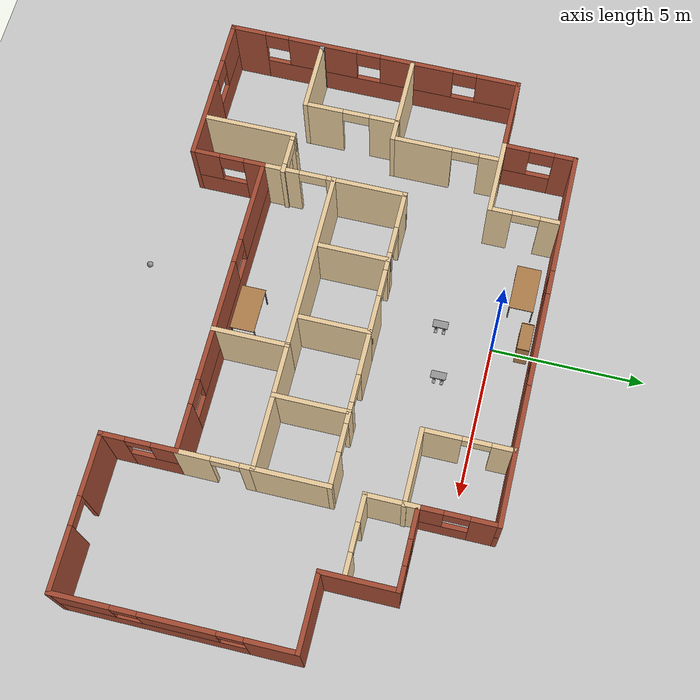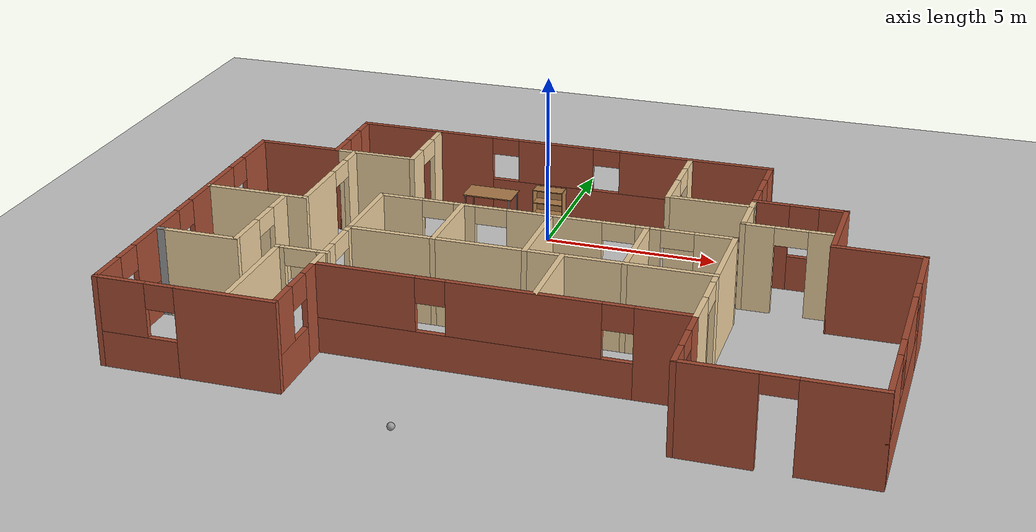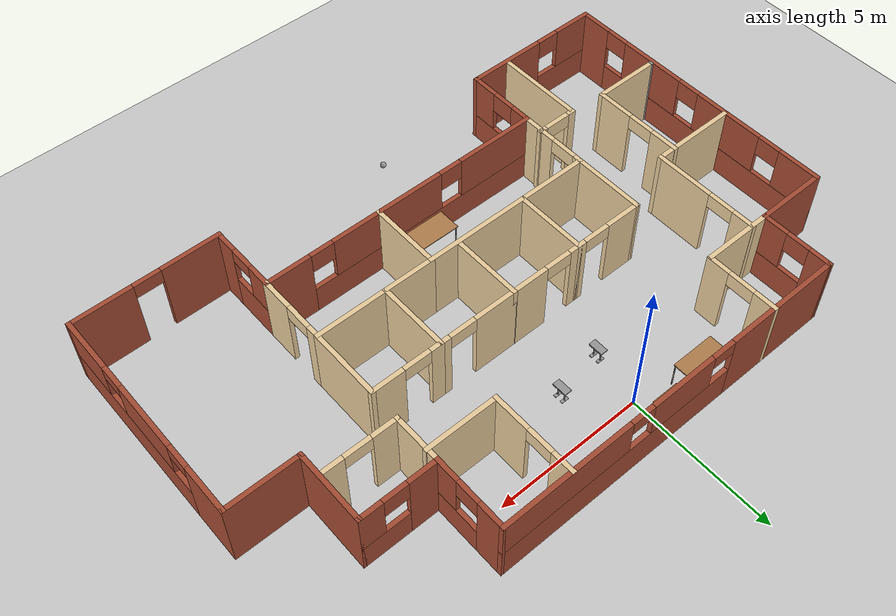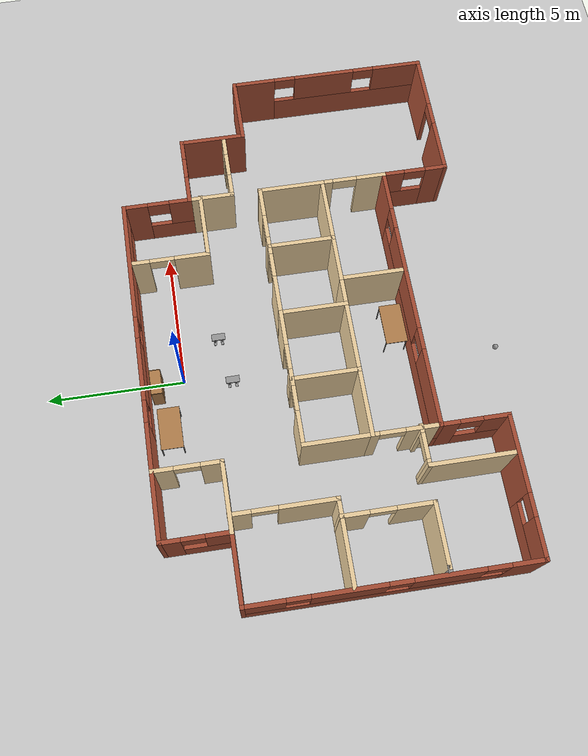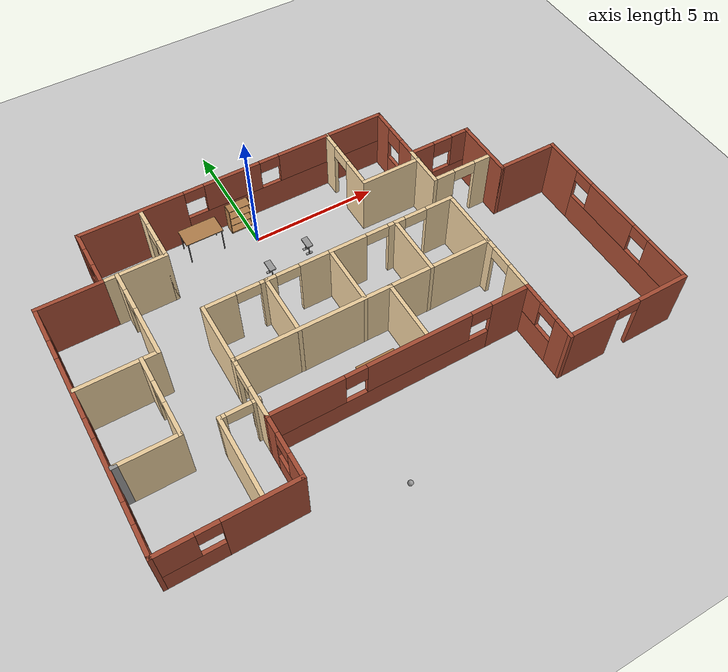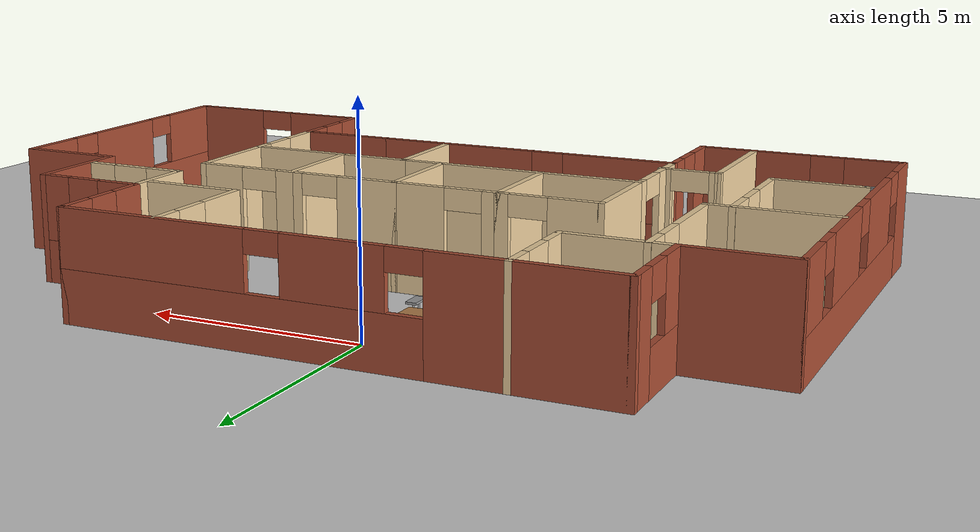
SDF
<sdf version="1.6">
 <world name="default">
  <plugin name="welcome_message" filename="libwelcome_message.so"/>
  <light name="sun" type="directional">
   <pose>0 0 10 0 -0 0</pose>
   <diffuse>0.8 0.8 0.8 1</diffuse>
   <specular>0.1 0.1 0.1 1</specular>
   <attenuation>
    <range>1000</range>
    <constant>0.9</constant>
    <linear>0.01</linear>
    <quadratic>0.001</quadratic>
   </attenuation>
   <direction>-0.5 0.5 -1</direction>
  </light>
  <model name="ground_plane">
   <static>1</static>
   <link name="link">
    <collision name="collision">
     <geometry><plane><normal>0 0 1</normal><size>100 100</size></plane></geometry>
     <surface>
      <contact><collide_bitmask>65535</collide_bitmask></contact>
      <friction><ode><mu>100</mu><mu2>50</mu2></ode></friction>
     </surface>
    </collision>
    <visual name="visual">
     <cast_shadows>0</cast_shadows>
     <geometry><plane><normal>0 0 1</normal><size>100 100</size></plane></geometry>
     <material>
      <script><uri>file://media/materials/scripts/gazebo.material</uri><name>Gazebo/Grey</name></script>
     </material>
    </visual>
   </link>
  </model>
  <gravity>0 0 -9.8</gravity>
  <magnetic_field>6e-06 2.3e-05 -4.2e-05</magnetic_field>
  <atmosphere type="adiabatic"/>
  <physics name="default_physics" default="0" type="ode">
   <max_step_size>0.001</max_step_size>
   <real_time_factor>1</real_time_factor>
   <real_time_update_rate>1000</real_time_update_rate>
  </physics>
  <scene><ambient>0.4 0.4 0.4 1</ambient><background>0.7 0.7 0.7 1</background><shadows>1</shadows></scene>
  <spherical_coordinates>
   <surface_model>EARTH_WGS84</surface_model>
   <latitude_deg>0</latitude_deg>
   <longitude_deg>0</longitude_deg>
   <elevation>0</elevation>
   <heading_deg>0</heading_deg>
  </spherical_coordinates>
  <model name="HumanoidRobot">
   <link name="link_0">
    <pose>0 0 0.297 0 -0 0</pose>
    <inertial>
     <mass>1</mass>
     <inertia>
      <ixx>0.166667</ixx>
      <ixy>0</ixy>
      <ixz>0</ixz>
      <iyy>0.166667</iyy>
      <iyz>0</iyz>
      <izz>0.166667</izz>
     </inertia>
    </inertial>
    <visual name="visual">
     <geometry><box><size>0.25 0.5 0.05</size></box></geometry>
     <material>
      <lighting>1</lighting>
      <script><uri>file://media/materials/scripts/gazebo.material</uri><name>Gazebo/Grey</name></script>
      <shader type="pixel"><normal_map>__default__</normal_map></shader>
      <ambient>0.3 0.3 0.3 1</ambient>
      <diffuse>0.7 0.7 0.7 1</diffuse>
      <specular>0.01 0.01 0.01 1</specular>
      <emissive>0 0 0 1</emissive>
     </material>
    </visual>
    <collision name="collision">
     <geometry><box><size>0.25 0.5 0.05</size></box></geometry>
     <surface>
      <friction>
       <ode><mu>1</mu><mu2>1</mu2><fdir1>0 0 0</fdir1><slip1>0</slip1><slip2>0</slip2></ode>
       <torsional>
        <coefficient>1</coefficient>
        <patch_radius>0</patch_radius>
        <surface_radius>0</surface_radius>
        <use_patch_radius>1</use_patch_radius>
        <ode><slip>0</slip></ode>
       </torsional>
      </friction>
      <bounce><restitution_coefficient>0</restitution_coefficient><threshold>1e+06</threshold></bounce>
      <contact>
       <collide_without_contact>0</collide_without_contact>
       <collide_without_contact_bitmask>1</collide_without_contact_bitmask>
       <collide_bitmask>1</collide_bitmask>
       <ode>
        <soft_cfm>0</soft_cfm>
        <soft_erp>0.2</soft_erp>
        <kp>1e+13</kp>
        <kd>1</kd>
        <max_vel>0.01</max_vel>
        <min_depth>0</min_depth>
       </ode>
       <bullet>
        <split_impulse>1</split_impulse>
        <split_impulse_penetration_threshold>-0.01</split_impulse_penetration_threshold>
        <soft_cfm>0</soft_cfm>
        <soft_erp>0.2</soft_erp>
        <kp>1e+13</kp>
        <kd>1</kd>
       </bullet>
      </contact>
     </surface>
    </collision>
   </link>
   <link name="link_1">
    <pose>0 -0.13 -0.193 0 -0 0</pose>
    <inertial>
     <mass>1</mass>
     <inertia>
      <ixx>0.166667</ixx>
      <ixy>0</ixy>
      <ixz>0</ixz>
      <iyy>0.166667</iyy>
      <iyz>0</iyz>
      <izz>0.166667</izz>
     </inertia>
    </inertial>
    <visual name="visual">
     <geometry><box><size>0.25 0.1 0.02</size></box></geometry>
     <material>
      <lighting>1</lighting>
      <script><uri>file://media/materials/scripts/gazebo.material</uri><name>Gazebo/Grey</name></script>
      <shader type="pixel"><normal_map>__default__</normal_map></shader>
      <ambient>0.3 0.3 0.3 1</ambient>
      <diffuse>0.7 0.7 0.7 1</diffuse>
      <specular>0.01 0.01 0.01 1</specular>
      <emissive>0 0 0 1</emissive>
     </material>
    </visual>
    <collision name="collision">
     <geometry><box><size>0.25 0.1 0.02</size></box></geometry>
     <surface>
      <friction>
       <ode><mu>1</mu><mu2>1</mu2><fdir1>0 0 0</fdir1><slip1>0</slip1><slip2>0</slip2></ode>
       <torsional>
        <coefficient>1</coefficient>
        <patch_radius>0</patch_radius>
        <surface_radius>0</surface_radius>
        <use_patch_radius>1</use_patch_radius>
        <ode><slip>0</slip></ode>
       </torsional>
      </friction>
      <bounce><restitution_coefficient>0</restitution_coefficient><threshold>1e+06</threshold></bounce>
      <contact>
       <collide_without_contact>0</collide_without_contact>
       <collide_without_contact_bitmask>1</collide_without_contact_bitmask>
       <collide_bitmask>1</collide_bitmask>
       <ode>
        <soft_cfm>0</soft_cfm>
        <soft_erp>0.2</soft_erp>
        <kp>1e+13</kp>
        <kd>1</kd>
        <max_vel>0.01</max_vel>
        <min_depth>0</min_depth>
       </ode>
       <bullet>
        <split_impulse>1</split_impulse>
        <split_impulse_penetration_threshold>-0.01</split_impulse_penetration_threshold>
        <soft_cfm>0</soft_cfm>
        <soft_erp>0.2</soft_erp>
        <kp>1e+13</kp>
        <kd>1</kd>
       </bullet>
      </contact>
     </surface>
    </collision>
   </link>
   <link name="link_1_clone">
    <pose>0 0.13 -0.193 0 -0 0</pose>
    <inertial>
     <mass>1</mass>
     <inertia>
      <ixx>0.166667</ixx>
      <ixy>0</ixy>
      <ixz>0</ixz>
      <iyy>0.166667</iyy>
      <iyz>0</iyz>
      <izz>0.166667</izz>
     </inertia>
    </inertial>
    <visual name="visual">
     <geometry><box><size>0.25 0.1 0.02</size></box></geometry>
     <material>
      <lighting>1</lighting>
      <script><uri>file://media/materials/scripts/gazebo.material</uri><name>Gazebo/Grey</name></script>
      <shader type="pixel"><normal_map>__default__</normal_map></shader>
      <ambient>0.3 0.3 0.3 1</ambient>
      <diffuse>0.7 0.7 0.7 1</diffuse>
      <specular>0.01 0.01 0.01 1</specular>
      <emissive>0 0 0 1</emissive>
     </material>
    </visual>
    <collision name="collision">
     <geometry><box><size>0.25 0.1 0.02</size></box></geometry>
     <surface>
      <friction>
       <ode><mu>1</mu><mu2>1</mu2><fdir1>0 0 0</fdir1><slip1>0</slip1><slip2>0</slip2></ode>
       <torsional>
        <coefficient>1</coefficient>
        <patch_radius>0</patch_radius>
        <surface_radius>0</surface_radius>
        <use_patch_radius>1</use_patch_radius>
        <ode><slip>0</slip></ode>
       </torsional>
      </friction>
      <bounce><restitution_coefficient>0</restitution_coefficient><threshold>1e+06</threshold></bounce>
      <contact>
       <collide_without_contact>0</collide_without_contact>
       <collide_without_contact_bitmask>1</collide_without_contact_bitmask>
       <collide_bitmask>1</collide_bitmask>
       <ode>
        <soft_cfm>0</soft_cfm>
        <soft_erp>0.2</soft_erp>
        <kp>1e+13</kp>
        <kd>1</kd>
        <max_vel>0.01</max_vel>
        <min_depth>0</min_depth>
       </ode>
       <bullet>
        <split_impulse>1</split_impulse>
        <split_impulse_penetration_threshold>-0.01</split_impulse_penetration_threshold>
        <soft_cfm>0</soft_cfm>
        <soft_erp>0.2</soft_erp>
        <kp>1e+13</kp>
        <kd>1</kd>
       </bullet>
      </contact>
     </surface>
    </collision>
   </link>
   <link name="link_2">
    <pose>0 -0.13 0.0445 0 -0 0</pose>
    <inertial>
     <mass>1</mass>
     <inertia><ixx>0.145833</ixx><ixy>0</ixy><ixz>0</ixz><iyy>0.145833</iyy><iyz>0</iyz><izz>0.125</izz></inertia>
    </inertial>
    <visual name="visual">
     <geometry><cylinder><radius>0.02</radius><length>0.455</length></cylinder></geometry>
     <material>
      <lighting>1</lighting>
      <script><uri>file://media/materials/scripts/gazebo.material</uri><name>Gazebo/Grey</name></script>
      <shader type="pixel"><normal_map>__default__</normal_map></shader>
      <ambient>0.3 0.3 0.3 1</ambient>
      <diffuse>0.7 0.7 0.7 1</diffuse>
      <specular>0.01 0.01 0.01 1</specular>
      <emissive>0 0 0 1</emissive>
     </material>
    </visual>
    <collision name="collision">
     <geometry><cylinder><radius>0.02</radius><length>0.455</length></cylinder></geometry>
     <surface>
      <friction>
       <ode><mu>1</mu><mu2>1</mu2><fdir1>0 0 0</fdir1><slip1>0</slip1><slip2>0</slip2></ode>
       <torsional>
        <coefficient>1</coefficient>
        <patch_radius>0</patch_radius>
        <surface_radius>0</surface_radius>
        <use_patch_radius>1</use_patch_radius>
        <ode><slip>0</slip></ode>
       </torsional>
      </friction>
      <bounce><restitution_coefficient>0</restitution_coefficient><threshold>1e+06</threshold></bounce>
      <contact>
       <collide_without_contact>0</collide_without_contact>
       <collide_without_contact_bitmask>1</collide_without_contact_bitmask>
       <collide_bitmask>1</collide_bitmask>
       <ode>
        <soft_cfm>0</soft_cfm>
        <soft_erp>0.2</soft_erp>
        <kp>1e+13</kp>
        <kd>1</kd>
        <max_vel>0.01</max_vel>
        <min_depth>0</min_depth>
       </ode>
       <bullet>
        <split_impulse>1</split_impulse>
        <split_impulse_penetration_threshold>-0.01</split_impulse_penetration_threshold>
        <soft_cfm>0</soft_cfm>
        <soft_erp>0.2</soft_erp>
        <kp>1e+13</kp>
        <kd>1</kd>
       </bullet>
      </contact>
     </surface>
    </collision>
   </link>
   <link name="link_2_clone">
    <pose>0 0.13 0.0445 0 -0 0</pose>
    <inertial>
     <mass>1</mass>
     <inertia><ixx>0.145833</ixx><ixy>0</ixy><ixz>0</ixz><iyy>0.145833</iyy><iyz>0</iyz><izz>0.125</izz></inertia>
    </inertial>
    <visual name="visual">
     <geometry><cylinder><radius>0.02</radius><length>0.455</length></cylinder></geometry>
     <material>
      <lighting>1</lighting>
      <script><uri>file://media/materials/scripts/gazebo.material</uri><name>Gazebo/Grey</name></script>
      <shader type="pixel"><normal_map>__default__</normal_map></shader>
      <ambient>0.3 0.3 0.3 1</ambient>
      <diffuse>0.7 0.7 0.7 1</diffuse>
      <specular>0.01 0.01 0.01 1</specular>
      <emissive>0 0 0 1</emissive>
     </material>
    </visual>
    <collision name="collision">
     <geometry><cylinder><radius>0.02</radius><length>0.455</length></cylinder></geometry>
     <surface>
      <friction>
       <ode><mu>1</mu><mu2>1</mu2><fdir1>0 0 0</fdir1><slip1>0</slip1><slip2>0</slip2></ode>
       <torsional>
        <coefficient>1</coefficient>
        <patch_radius>0</patch_radius>
        <surface_radius>0</surface_radius>
        <use_patch_radius>1</use_patch_radius>
        <ode><slip>0</slip></ode>
       </torsional>
      </friction>
      <bounce><restitution_coefficient>0</restitution_coefficient><threshold>1e+06</threshold></bounce>
      <contact>
       <collide_without_contact>0</collide_without_contact>
       <collide_without_contact_bitmask>1</collide_without_contact_bitmask>
       <collide_bitmask>1</collide_bitmask>
       <ode>
        <soft_cfm>0</soft_cfm>
        <soft_erp>0.2</soft_erp>
        <kp>1e+13</kp>
        <kd>1</kd>
        <max_vel>0.01</max_vel>
        <min_depth>0</min_depth>
       </ode>
       <bullet>
        <split_impulse>1</split_impulse>
        <split_impulse_penetration_threshold>-0.01</split_impulse_penetration_threshold>
        <soft_cfm>0</soft_cfm>
        <soft_erp>0.2</soft_erp>
        <kp>1e+13</kp>
        <kd>1</kd>
       </bullet>
      </contact>
     </surface>
    </collision>
   </link>
   <joint name="link_0_JOINT_0" type="fixed">
    <parent>link_0</parent>
    <child>link_2</child>
    <physics>
     <ode><limit><cfm>0</cfm><erp>0.2</erp></limit><suspension><cfm>0</cfm><erp>0.2</erp></suspension></ode>
    </physics>
   </joint>
   <joint name="link_0_JOINT_1" type="fixed">
    <parent>link_0</parent>
    <child>link_2_clone</child>
    <physics>
     <ode><limit><cfm>0</cfm><erp>0.2</erp></limit><suspension><cfm>0</cfm><erp>0.2</erp></suspension></ode>
    </physics>
   </joint>
   <joint name="link_2_JOINT_2" type="fixed">
    <parent>link_2</parent>
    <child>link_1</child>
    <physics>
     <ode><limit><cfm>0</cfm><erp>0.2</erp></limit><suspension><cfm>0</cfm><erp>0.2</erp></suspension></ode>
    </physics>
   </joint>
   <joint name="link_2_clone_JOINT_3" type="fixed">
    <parent>link_2_clone</parent>
    <child>link_1_clone</child>
    <physics>
     <ode><limit><cfm>0</cfm><erp>0.2</erp></limit><suspension><cfm>0</cfm><erp>0.2</erp></suspension></ode>
    </physics>
   </joint>
   <static>0</static>
   <pose>1.40793 -1.46037 0.203 -2e-06 -0 0.002952</pose>
  </model>
  <model name="Building">
   <pose>1.29293 -4.72878 0 0 -0 0</pose>
   <link name="Wall_1">
    <pose>-1.24984 6.0735 0 0 0 -3.9e-05</pose>
    <visual name="Wall_1_Visual_0">
     <pose>-4.19104 0 1.25 0 -0 0</pose>
     <geometry><box><size>4.11792 0.15 2.5</size></box></geometry>
     <material>
      <script><uri>file://media/materials/scripts/gazebo.material</uri><name>Gazebo/Bricks</name></script>
      <ambient>1 1 1 1</ambient>
     </material>
     <meta><layer>0</layer></meta>
    </visual>
    <collision name="Wall_1_Collision_0">
     <geometry><box><size>4.11792 0.15 2.5</size></box></geometry>
     <pose>-4.19104 0 1.25 0 -0 0</pose>
    </collision>
    <visual name="Wall_1_Visual_1">
     <pose>2.05896 0 0.6 0 -0 0</pose>
     <geometry><box><size>8.38208 0.15 1.2</size></box></geometry>
     <material>
      <script><uri>file://media/materials/scripts/gazebo.material</uri><name>Gazebo/Bricks</name></script>
      <ambient>1 1 1 1</ambient>
     </material>
     <meta><layer>0</layer></meta>
    </visual>
    <collision name="Wall_1_Collision_1">
     <geometry><box><size>8.38208 0.15 1.2</size></box></geometry>
     <pose>2.05896 0 0.6 0 -0 0</pose>
    </collision>
    <visual name="Wall_1_Visual_2">
     <pose>-0.189268 0 1.85 0 -0 0</pose>
     <geometry><box><size>2.28562 0.15 1.3</size></box></geometry>
     <material>
      <script><uri>file://media/materials/scripts/gazebo.material</uri><name>Gazebo/Bricks</name></script>
      <ambient>1 1 1 1</ambient>
     </material>
     <meta><layer>0</layer></meta>
    </visual>
    <collision name="Wall_1_Collision_2">
     <geometry><box><size>2.28562 0.15 1.3</size></box></geometry>
     <pose>-0.189268 0 1.85 0 -0 0</pose>
    </collision>
    <visual name="Wall_1_Visual_3">
     <pose>4.00177 0 1.85 0 -0 0</pose>
     <geometry><box><size>4.49646 0.15 1.3</size></box></geometry>
     <material>
      <script><uri>file://media/materials/scripts/gazebo.material</uri><name>Gazebo/Bricks</name></script>
      <ambient>1 1 1 1</ambient>
     </material>
     <meta><layer>0</layer></meta>
    </visual>
    <collision name="Wall_1_Collision_3">
     <geometry><box><size>4.49646 0.15 1.3</size></box></geometry>
     <pose>4.00177 0 1.85 0 -0 0</pose>
    </collision>
    <visual name="Wall_1_Visual_4">
     <pose>-1.73208 0 2.25 0 -0 0</pose>
     <geometry><box><size>0.8 0.15 0.5</size></box></geometry>
     <material>
      <script><uri>file://media/materials/scripts/gazebo.material</uri><name>Gazebo/Bricks</name></script>
      <ambient>1 1 1 1</ambient>
     </material>
     <meta><layer>0</layer></meta>
    </visual>
    <collision name="Wall_1_Collision_4">
     <geometry><box><size>0.8 0.15 0.5</size></box></geometry>
     <pose>-1.73208 0 2.25 0 -0 0</pose>
    </collision>
    <visual name="Wall_1_Visual_5">
     <pose>1.35354 0 2.25 0 -0 0</pose>
     <geometry><box><size>0.8 0.15 0.5</size></box></geometry>
     <material>
      <script><uri>file://media/materials/scripts/gazebo.material</uri><name>Gazebo/Bricks</name></script>
      <ambient>1 1 1 1</ambient>
     </material>
     <meta><layer>0</layer></meta>
    </visual>
    <collision name="Wall_1_Collision_5">
     <geometry><box><size>0.8 0.15 0.5</size></box></geometry>
     <pose>1.35354 0 2.25 0 -0 0</pose>
    </collision>
   </link>
   <link name="Wall_10">
    <collision name="Wall_10_Collision">
     <geometry><box><size>2.5 0.15 2.5</size></box></geometry>
     <pose>0 0 1.25 0 -0 0</pose>
    </collision>
    <visual name="Wall_10_Visual">
     <pose>0 0 1.25 0 -0 0</pose>
     <geometry><box><size>2.5 0.15 2.5</size></box></geometry>
     <material>
      <script><uri>file://media/materials/scripts/gazebo.material</uri><name>Gazebo/Bricks</name></script>
      <ambient>1 1 1 1</ambient>
     </material>
     <meta><layer>0</layer></meta>
    </visual>
    <pose>8.6 1.27626 0 0 -0 0</pose>
   </link>
   <link name="Wall_12">
    <pose>9.775 -2.39874 0 0 0 -1.5708</pose>
    <visual name="Wall_12_Visual_0">
     <pose>-2.91894 0 1.25 0 -0 0</pose>
     <geometry><box><size>1.66211 0.15 2.5</size></box></geometry>
     <material>
      <script><uri>file://media/materials/scripts/gazebo.material</uri><name>Gazebo/Bricks</name></script>
      <ambient>1 1 1 1</ambient>
     </material>
     <meta><layer>0</layer></meta>
    </visual>
    <collision name="Wall_12_Collision_0">
     <geometry><box><size>1.66211 0.15 2.5</size></box></geometry>
     <pose>-2.91894 0 1.25 0 -0 0</pose>
    </collision>
    <visual name="Wall_12_Visual_1">
     <pose>0.831055 0 0.6 0 -0 0</pose>
     <geometry><box><size>5.83789 0.15 1.2</size></box></geometry>
     <material>
      <script><uri>file://media/materials/scripts/gazebo.material</uri><name>Gazebo/Bricks</name></script>
      <ambient>1 1 1 1</ambient>
     </material>
     <meta><layer>0</layer></meta>
    </visual>
    <collision name="Wall_12_Collision_1">
     <geometry><box><size>5.83789 0.15 1.2</size></box></geometry>
     <pose>0.831055 0 0.6 0 -0 0</pose>
    </collision>
    <visual name="Wall_12_Visual_2">
     <pose>-0.118478 0 1.85 0 -0 0</pose>
     <geometry><box><size>2.33882 0.15 1.3</size></box></geometry>
     <material>
      <script><uri>file://media/materials/scripts/gazebo.material</uri><name>Gazebo/Bricks</name></script>
      <ambient>1 1 1 1</ambient>
     </material>
     <meta><layer>0</layer></meta>
    </visual>
    <collision name="Wall_12_Collision_2">
     <geometry><box><size>2.33882 0.15 1.3</size></box></geometry>
     <pose>-0.118478 0 1.85 0 -0 0</pose>
    </collision>
    <visual name="Wall_12_Visual_3">
     <pose>2.80047 0 1.85 0 -0 0</pose>
     <geometry><box><size>1.89907 0.15 1.3</size></box></geometry>
     <material>
      <script><uri>file://media/materials/scripts/gazebo.material</uri><name>Gazebo/Bricks</name></script>
      <ambient>1 1 1 1</ambient>
     </material>
     <meta><layer>0</layer></meta>
    </visual>
    <collision name="Wall_12_Collision_3">
     <geometry><box><size>1.89907 0.15 1.3</size></box></geometry>
     <pose>2.80047 0 1.85 0 -0 0</pose>
    </collision>
    <visual name="Wall_12_Visual_4">
     <pose>-1.68789 0 2.25 0 -0 0</pose>
     <geometry><box><size>0.8 0.15 0.5</size></box></geometry>
     <material>
      <script><uri>file://media/materials/scripts/gazebo.material</uri><name>Gazebo/Bricks</name></script>
      <ambient>1 1 1 1</ambient>
     </material>
     <meta><layer>0</layer></meta>
    </visual>
    <collision name="Wall_12_Collision_4">
     <geometry><box><size>0.8 0.15 0.5</size></box></geometry>
     <pose>-1.68789 0 2.25 0 -0 0</pose>
    </collision>
    <visual name="Wall_12_Visual_5">
     <pose>1.45093 0 2.25 0 -0 0</pose>
     <geometry><box><size>0.8 0.15 0.5</size></box></geometry>
     <material>
      <script><uri>file://media/materials/scripts/gazebo.material</uri><name>Gazebo/Bricks</name></script>
      <ambient>1 1 1 1</ambient>
     </material>
     <meta><layer>0</layer></meta>
    </visual>
    <collision name="Wall_12_Collision_5">
     <geometry><box><size>0.8 0.15 0.5</size></box></geometry>
     <pose>1.45093 0 2.25 0 -0 0</pose>
    </collision>
   </link>
   <link name="Wall_14">
    <pose>7.35 -6.07374 0 0 -0 3.14159</pose>
    <visual name="Wall_14_Visual_0">
     <pose>-1.46948 0 1.25 0 -0 0</pose>
     <geometry><box><size>2.06104 0.15 2.5</size></box></geometry>
     <material>
      <script><uri>file://media/materials/scripts/gazebo.material</uri><name>Gazebo/Bricks</name></script>
      <ambient>1 1 1 1</ambient>
     </material>
     <meta><layer>0</layer></meta>
    </visual>
    <collision name="Wall_14_Collision_0">
     <geometry><box><size>2.06104 0.15 2.5</size></box></geometry>
     <pose>-1.46948 0 1.25 0 -0 0</pose>
    </collision>
    <visual name="Wall_14_Visual_1">
     <pose>1.48052 0 1.25 0 -0 0</pose>
     <geometry><box><size>2.03896 0.15 2.5</size></box></geometry>
     <material>
      <script><uri>file://media/materials/scripts/gazebo.material</uri><name>Gazebo/Bricks</name></script>
      <ambient>1 1 1 1</ambient>
     </material>
     <meta><layer>0</layer></meta>
    </visual>
    <collision name="Wall_14_Collision_1">
     <geometry><box><size>2.03896 0.15 2.5</size></box></geometry>
     <pose>1.48052 0 1.25 0 -0 0</pose>
    </collision>
    <visual name="Wall_14_Visual_2">
     <pose>0.011044 0 2.25 0 -0 0</pose>
     <geometry><box><size>0.9 0.15 0.5</size></box></geometry>
     <material>
      <script><uri>file://media/materials/scripts/gazebo.material</uri><name>Gazebo/Bricks</name></script>
      <ambient>1 1 1 1</ambient>
     </material>
     <meta><layer>0</layer></meta>
    </visual>
    <collision name="Wall_14_Collision_2">
     <geometry><box><size>0.9 0.15 0.5</size></box></geometry>
     <pose>0.011044 0 2.25 0 -0 0</pose>
    </collision>
   </link>
   <link name="Wall_16">
    <pose>4.925 -4.89874 0 0 -0 1.5708</pose>
    <visual name="Wall_16_Visual_0">
     <pose>-0.832471 0 1.25 0 -0 0</pose>
     <geometry><box><size>0.835058 0.15 2.5</size></box></geometry>
     <material>
      <script><uri>file://media/materials/scripts/gazebo.material</uri><name>Gazebo/Bricks</name></script>
      <ambient>1 1 1 1</ambient>
     </material>
     <meta><layer>0</layer></meta>
    </visual>
    <collision name="Wall_16_Collision_0">
     <geometry><box><size>0.835058 0.15 2.5</size></box></geometry>
     <pose>-0.832471 0 1.25 0 -0 0</pose>
    </collision>
    <visual name="Wall_16_Visual_1">
     <pose>0.417529 0 0.6 0 -0 0</pose>
     <geometry><box><size>1.66494 0.15 1.2</size></box></geometry>
     <material>
      <script><uri>file://media/materials/scripts/gazebo.material</uri><name>Gazebo/Bricks</name></script>
      <ambient>1 1 1 1</ambient>
     </material>
     <meta><layer>0</layer></meta>
    </visual>
    <collision name="Wall_16_Collision_1">
     <geometry><box><size>1.66494 0.15 1.2</size></box></geometry>
     <pose>0.417529 0 0.6 0 -0 0</pose>
    </collision>
    <visual name="Wall_16_Visual_2">
     <pose>0.817529 0 1.85 0 -0 0</pose>
     <geometry><box><size>0.864942 0.15 1.3</size></box></geometry>
     <material>
      <script><uri>file://media/materials/scripts/gazebo.material</uri><name>Gazebo/Bricks</name></script>
      <ambient>1 1 1 1</ambient>
     </material>
     <meta><layer>0</layer></meta>
    </visual>
    <collision name="Wall_16_Collision_2">
     <geometry><box><size>0.864942 0.15 1.3</size></box></geometry>
     <pose>0.817529 0 1.85 0 -0 0</pose>
    </collision>
    <visual name="Wall_16_Visual_3">
     <pose>-0.014942 0 2.25 0 -0 0</pose>
     <geometry><box><size>0.8 0.15 0.5</size></box></geometry>
     <material>
      <script><uri>file://media/materials/scripts/gazebo.material</uri><name>Gazebo/Bricks</name></script>
      <ambient>1 1 1 1</ambient>
     </material>
     <meta><layer>0</layer></meta>
    </visual>
    <collision name="Wall_16_Collision_3">
     <geometry><box><size>0.8 0.15 0.5</size></box></geometry>
     <pose>-0.014942 0 2.25 0 -0 0</pose>
    </collision>
   </link>
   <link name="Wall_18">
    <pose>1e-06 -3.72374 0 0 -0 3.14159</pose>
    <visual name="Wall_18_Visual_0">
     <pose>-4.21486 0 1.25 0 -0 0</pose>
     <geometry><box><size>1.57028 0.15 2.5</size></box></geometry>
     <material>
      <script><uri>file://media/materials/scripts/gazebo.material</uri><name>Gazebo/Bricks</name></script>
      <ambient>1 1 1 1</ambient>
     </material>
     <meta><layer>0</layer></meta>
    </visual>
    <collision name="Wall_18_Collision_0">
     <geometry><box><size>1.57028 0.15 2.5</size></box></geometry>
     <pose>-4.21486 0 1.25 0 -0 0</pose>
    </collision>
    <visual name="Wall_18_Visual_1">
     <pose>0.785138 0 0.5 0 -0 0</pose>
     <geometry><box><size>8.42972 0.15 1</size></box></geometry>
     <material>
      <script><uri>file://media/materials/scripts/gazebo.material</uri><name>Gazebo/Bricks</name></script>
      <ambient>1 1 1 1</ambient>
     </material>
     <meta><layer>0</layer></meta>
    </visual>
    <collision name="Wall_18_Collision_1">
     <geometry><box><size>8.42972 0.15 1</size></box></geometry>
     <pose>0.785138 0 0.5 0 -0 0</pose>
    </collision>
    <visual name="Wall_18_Visual_2">
     <pose>-0.622407 0 1.75 0 -0 0</pose>
     <geometry><box><size>4.01464 0.15 1.5</size></box></geometry>
     <material>
      <script><uri>file://media/materials/scripts/gazebo.material</uri><name>Gazebo/Bricks</name></script>
      <ambient>1 1 1 1</ambient>
     </material>
     <meta><layer>0</layer></meta>
    </visual>
    <collision name="Wall_18_Collision_2">
     <geometry><box><size>4.01464 0.15 1.5</size></box></geometry>
     <pose>-0.622407 0 1.75 0 -0 0</pose>
    </collision>
    <visual name="Wall_18_Visual_3">
     <pose>3.59246 0 1.75 0 -0 0</pose>
     <geometry><box><size>2.81509 0.15 1.5</size></box></geometry>
     <material>
      <script><uri>file://media/materials/scripts/gazebo.material</uri><name>Gazebo/Bricks</name></script>
      <ambient>1 1 1 1</ambient>
     </material>
     <meta><layer>0</layer></meta>
    </visual>
    <collision name="Wall_18_Collision_3">
     <geometry><box><size>2.81509 0.15 1.5</size></box></geometry>
     <pose>3.59246 0 1.75 0 -0 0</pose>
    </collision>
    <visual name="Wall_18_Visual_4">
     <pose>-3.02973 0 2.15 0 -0 0</pose>
     <geometry><box><size>0.8 0.15 0.7</size></box></geometry>
     <material>
      <script><uri>file://media/materials/scripts/gazebo.material</uri><name>Gazebo/Bricks</name></script>
      <ambient>1 1 1 1</ambient>
     </material>
     <meta><layer>0</layer></meta>
    </visual>
    <collision name="Wall_18_Collision_4">
     <geometry><box><size>0.8 0.15 0.7</size></box></geometry>
     <pose>-3.02973 0 2.15 0 -0 0</pose>
    </collision>
    <visual name="Wall_18_Visual_5">
     <pose>1.78491 0 2.15 0 -0 0</pose>
     <geometry><box><size>0.8 0.15 0.7</size></box></geometry>
     <material>
      <script><uri>file://media/materials/scripts/gazebo.material</uri><name>Gazebo/Bricks</name></script>
      <ambient>1 1 1 1</ambient>
     </material>
     <meta><layer>0</layer></meta>
    </visual>
    <collision name="Wall_18_Collision_5">
     <geometry><box><size>0.8 0.15 0.7</size></box></geometry>
     <pose>1.78491 0 2.15 0 -0 0</pose>
    </collision>
   </link>
   <link name="Wall_2">
    <pose>4.925 4.84976 0 0 0 -1.5708</pose>
    <visual name="Wall_2_Visual_0">
     <pose>-0.822065 0 1.25 0 -0 0</pose>
     <geometry><box><size>0.952869 0.15 2.5</size></box></geometry>
     <material>
      <script><uri>file://media/materials/scripts/gazebo.material</uri><name>Gazebo/Bricks</name></script>
      <ambient>1 1 1 1</ambient>
     </material>
     <meta><layer>0</layer></meta>
    </visual>
    <collision name="Wall_2_Collision_0">
     <geometry><box><size>0.952869 0.15 2.5</size></box></geometry>
     <pose>-0.822065 0 1.25 0 -0 0</pose>
    </collision>
    <visual name="Wall_2_Visual_1">
     <pose>0.476435 0 0.5 0 -0 0</pose>
     <geometry><box><size>1.64413 0.15 1</size></box></geometry>
     <material>
      <script><uri>file://media/materials/scripts/gazebo.material</uri><name>Gazebo/Bricks</name></script>
      <ambient>1 1 1 1</ambient>
     </material>
     <meta><layer>0</layer></meta>
    </visual>
    <collision name="Wall_2_Collision_1">
     <geometry><box><size>1.64413 0.15 1</size></box></geometry>
     <pose>0.476435 0 0.5 0 -0 0</pose>
    </collision>
    <visual name="Wall_2_Visual_2">
     <pose>0.876435 0 1.75 0 -0 0</pose>
     <geometry><box><size>0.844131 0.15 1.5</size></box></geometry>
     <material>
      <script><uri>file://media/materials/scripts/gazebo.material</uri><name>Gazebo/Bricks</name></script>
      <ambient>1 1 1 1</ambient>
     </material>
     <meta><layer>0</layer></meta>
    </visual>
    <collision name="Wall_2_Collision_2">
     <geometry><box><size>0.844131 0.15 1.5</size></box></geometry>
     <pose>0.876435 0 1.75 0 -0 0</pose>
    </collision>
    <visual name="Wall_2_Visual_3">
     <pose>0.054369 0 2.15 0 -0 0</pose>
     <geometry><box><size>0.8 0.15 0.7</size></box></geometry>
     <material>
      <script><uri>file://media/materials/scripts/gazebo.material</uri><name>Gazebo/Bricks</name></script>
      <ambient>1 1 1 1</ambient>
     </material>
     <meta><layer>0</layer></meta>
    </visual>
    <collision name="Wall_2_Collision_3">
     <geometry><box><size>0.8 0.15 0.7</size></box></geometry>
     <pose>0.054369 0 2.15 0 -0 0</pose>
    </collision>
   </link>
   <link name="Wall_20">
    <pose>-7.42468 4.89874 0 0 0 -1.5708</pose>
    <visual name="Wall_20_Visual_0">
     <pose>-0.866423 0 1.25 0 -0 0</pose>
     <geometry><box><size>0.767154 0.15 2.5</size></box></geometry>
     <material>
      <script><uri>file://media/materials/scripts/gazebo.material</uri><name>Gazebo/Bricks</name></script>
      <ambient>1 1 1 1</ambient>
     </material>
     <meta><layer>0</layer></meta>
    </visual>
    <collision name="Wall_20_Collision_0">
     <geometry><box><size>0.767154 0.15 2.5</size></box></geometry>
     <pose>-0.866423 0 1.25 0 -0 0</pose>
    </collision>
    <visual name="Wall_20_Visual_1">
     <pose>0.383577 0 0.5 0 -0 0</pose>
     <geometry><box><size>1.73285 0.15 1</size></box></geometry>
     <material>
      <script><uri>file://media/materials/scripts/gazebo.material</uri><name>Gazebo/Bricks</name></script>
      <ambient>1 1 1 1</ambient>
     </material>
     <meta><layer>0</layer></meta>
    </visual>
    <collision name="Wall_20_Collision_1">
     <geometry><box><size>1.73285 0.15 1</size></box></geometry>
     <pose>0.383577 0 0.5 0 -0 0</pose>
    </collision>
    <visual name="Wall_20_Visual_2">
     <pose>0.783577 0 1.75 0 -0 0</pose>
     <geometry><box><size>0.932846 0.15 1.5</size></box></geometry>
     <material>
      <script><uri>file://media/materials/scripts/gazebo.material</uri><name>Gazebo/Bricks</name></script>
      <ambient>1 1 1 1</ambient>
     </material>
     <meta><layer>0</layer></meta>
    </visual>
    <collision name="Wall_20_Collision_2">
     <geometry><box><size>0.932846 0.15 1.5</size></box></geometry>
     <pose>0.783577 0 1.75 0 -0 0</pose>
    </collision>
    <visual name="Wall_20_Visual_3">
     <pose>-0.082846 0 2.15 0 -0 0</pose>
     <geometry><box><size>0.8 0.15 0.7</size></box></geometry>
     <material>
      <script><uri>file://media/materials/scripts/gazebo.material</uri><name>Gazebo/Bricks</name></script>
      <ambient>1 1 1 1</ambient>
     </material>
     <meta><layer>0</layer></meta>
    </visual>
    <collision name="Wall_20_Collision_3">
     <geometry><box><size>0.8 0.15 0.7</size></box></geometry>
     <pose>-0.082846 0 2.15 0 -0 0</pose>
    </collision>
   </link>
   <link name="Wall_22">
    <collision name="Wall_22_Collision">
     <geometry><box><size>2.5 0.15 2.5</size></box></geometry>
     <pose>0 0 1.25 0 -0 0</pose>
    </collision>
    <visual name="Wall_22_Visual">
     <pose>0 0 1.25 0 -0 0</pose>
     <geometry><box><size>2.5 0.15 2.5</size></box></geometry>
     <material>
      <script><uri>file://media/materials/scripts/gazebo.material</uri><name>Gazebo/Bricks</name></script>
      <ambient>1 1 1 1</ambient>
     </material>
     <meta><layer>0</layer></meta>
    </visual>
    <pose>-8.59968 3.72374 0 0 -0 3.14159</pose>
   </link>
   <link name="Wall_24">
    <pose>-4.925 -4.89874 0 0 0 -1.5708</pose>
    <visual name="Wall_24_Visual_0">
     <pose>-0.884029 0 1.25 0 -0 0</pose>
     <geometry><box><size>0.731941 0.15 2.5</size></box></geometry>
     <material>
      <script><uri>file://media/materials/scripts/gazebo.material</uri><name>Gazebo/Bricks</name></script>
      <ambient>1 1 1 1</ambient>
     </material>
     <meta><layer>0</layer></meta>
    </visual>
    <collision name="Wall_24_Collision_0">
     <geometry><box><size>0.731941 0.15 2.5</size></box></geometry>
     <pose>-0.884029 0 1.25 0 -0 0</pose>
    </collision>
    <visual name="Wall_24_Visual_1">
     <pose>0.365971 0 0.5 0 -0 0</pose>
     <geometry><box><size>1.76806 0.15 1</size></box></geometry>
     <material>
      <script><uri>file://media/materials/scripts/gazebo.material</uri><name>Gazebo/Bricks</name></script>
      <ambient>1 1 1 1</ambient>
     </material>
     <meta><layer>0</layer></meta>
    </visual>
    <collision name="Wall_24_Collision_1">
     <geometry><box><size>1.76806 0.15 1</size></box></geometry>
     <pose>0.365971 0 0.5 0 -0 0</pose>
    </collision>
    <visual name="Wall_24_Visual_2">
     <pose>0.765971 0 1.75 0 -0 0</pose>
     <geometry><box><size>0.968059 0.15 1.5</size></box></geometry>
     <material>
      <script><uri>file://media/materials/scripts/gazebo.material</uri><name>Gazebo/Bricks</name></script>
      <ambient>1 1 1 1</ambient>
     </material>
     <meta><layer>0</layer></meta>
    </visual>
    <collision name="Wall_24_Collision_2">
     <geometry><box><size>0.968059 0.15 1.5</size></box></geometry>
     <pose>0.765971 0 1.75 0 -0 0</pose>
    </collision>
    <visual name="Wall_24_Visual_3">
     <pose>-0.118059 0 2.15 0 -0 0</pose>
     <geometry><box><size>0.8 0.15 0.7</size></box></geometry>
     <material>
      <script><uri>file://media/materials/scripts/gazebo.material</uri><name>Gazebo/Bricks</name></script>
      <ambient>1 1 1 1</ambient>
     </material>
     <meta><layer>0</layer></meta>
    </visual>
    <collision name="Wall_24_Collision_3">
     <geometry><box><size>0.8 0.15 0.7</size></box></geometry>
     <pose>-0.118059 0 2.15 0 -0 0</pose>
    </collision>
   </link>
   <link name="Wall_26">
    <pose>-7.35 -6.07374 0 0 -0 3.14159</pose>
    <visual name="Wall_26_Visual_0">
     <pose>-1.12032 0 1.25 0 -0 0</pose>
     <geometry><box><size>2.75936 0.15 2.5</size></box></geometry>
     <material>
      <script><uri>file://media/materials/scripts/gazebo.material</uri><name>Gazebo/Bricks</name></script>
      <ambient>1 1 1 1</ambient>
     </material>
     <meta><layer>0</layer></meta>
    </visual>
    <collision name="Wall_26_Collision_0">
     <geometry><box><size>2.75936 0.15 2.5</size></box></geometry>
     <pose>-1.12032 0 1.25 0 -0 0</pose>
    </collision>
    <visual name="Wall_26_Visual_1">
     <pose>1.37968 0 0.5 0 -0 0</pose>
     <geometry><box><size>2.24064 0.15 1</size></box></geometry>
     <material>
      <script><uri>file://media/materials/scripts/gazebo.material</uri><name>Gazebo/Bricks</name></script>
      <ambient>1 1 1 1</ambient>
     </material>
     <meta><layer>0</layer></meta>
    </visual>
    <collision name="Wall_26_Collision_1">
     <geometry><box><size>2.24064 0.15 1</size></box></geometry>
     <pose>1.37968 0 0.5 0 -0 0</pose>
    </collision>
    <visual name="Wall_26_Visual_2">
     <pose>1.77968 0 1.75 0 -0 0</pose>
     <geometry><box><size>1.44064 0.15 1.5</size></box></geometry>
     <material>
      <script><uri>file://media/materials/scripts/gazebo.material</uri><name>Gazebo/Bricks</name></script>
      <ambient>1 1 1 1</ambient>
     </material>
     <meta><layer>0</layer></meta>
    </visual>
    <collision name="Wall_26_Collision_2">
     <geometry><box><size>1.44064 0.15 1.5</size></box></geometry>
     <pose>1.77968 0 1.75 0 -0 0</pose>
    </collision>
    <visual name="Wall_26_Visual_3">
     <pose>0.659358 0 2.15 0 -0 0</pose>
     <geometry><box><size>0.8 0.15 0.7</size></box></geometry>
     <material>
      <script><uri>file://media/materials/scripts/gazebo.material</uri><name>Gazebo/Bricks</name></script>
      <ambient>1 1 1 1</ambient>
     </material>
     <meta><layer>0</layer></meta>
    </visual>
    <collision name="Wall_26_Collision_3">
     <geometry><box><size>0.8 0.15 0.7</size></box></geometry>
     <pose>0.659358 0 2.15 0 -0 0</pose>
    </collision>
   </link>
   <link name="Wall_28">
    <pose>-9.77484 -1.175 0 0 -0 1.57076</pose>
    <visual name="Wall_28_Visual_0">
     <pose>-4.37001 0 1.25 0 -0 0</pose>
     <geometry><box><size>1.20746 0.15 2.5</size></box></geometry>
     <material>
      <script><uri>file://media/materials/scripts/gazebo.material</uri><name>Gazebo/Bricks</name></script>
      <ambient>1 1 1 1</ambient>
     </material>
     <meta><layer>0</layer></meta>
    </visual>
    <collision name="Wall_28_Collision_0">
     <geometry><box><size>1.20746 0.15 2.5</size></box></geometry>
     <pose>-4.37001 0 1.25 0 -0 0</pose>
    </collision>
    <visual name="Wall_28_Visual_1">
     <pose>0.603732 0 0.5 0 -0 0</pose>
     <geometry><box><size>8.74002 0.15 1</size></box></geometry>
     <material>
      <script><uri>file://media/materials/scripts/gazebo.material</uri><name>Gazebo/Bricks</name></script>
      <ambient>1 1 1 1</ambient>
     </material>
     <meta><layer>0</layer></meta>
    </visual>
    <collision name="Wall_28_Collision_1">
     <geometry><box><size>8.74002 0.15 1</size></box></geometry>
     <pose>0.603732 0 0.5 0 -0 0</pose>
    </collision>
    <visual name="Wall_28_Visual_2">
     <pose>-1.78357 0 1.75 0 -0 0</pose>
     <geometry><box><size>2.36542 0.15 1.5</size></box></geometry>
     <material>
      <script><uri>file://media/materials/scripts/gazebo.material</uri><name>Gazebo/Bricks</name></script>
      <ambient>1 1 1 1</ambient>
     </material>
     <meta><layer>0</layer></meta>
    </visual>
    <collision name="Wall_28_Collision_2">
     <geometry><box><size>2.36542 0.15 1.5</size></box></geometry>
     <pose>-1.78357 0 1.75 0 -0 0</pose>
    </collision>
    <visual name="Wall_28_Visual_3">
     <pose>1.44835 0 1.75 0 -0 0</pose>
     <geometry><box><size>2.49842 0.15 1.5</size></box></geometry>
     <material>
      <script><uri>file://media/materials/scripts/gazebo.material</uri><name>Gazebo/Bricks</name></script>
      <ambient>1 1 1 1</ambient>
     </material>
     <meta><layer>0</layer></meta>
    </visual>
    <collision name="Wall_28_Collision_3">
     <geometry><box><size>2.49842 0.15 1.5</size></box></geometry>
     <pose>1.44835 0 1.75 0 -0 0</pose>
    </collision>
    <visual name="Wall_28_Visual_4">
     <pose>4.23565 0 1.75 0 -0 0</pose>
     <geometry><box><size>1.47618 0.15 1.5</size></box></geometry>
     <material>
      <script><uri>file://media/materials/scripts/gazebo.material</uri><name>Gazebo/Bricks</name></script>
      <ambient>1 1 1 1</ambient>
     </material>
     <meta><layer>0</layer></meta>
    </visual>
    <collision name="Wall_28_Collision_4">
     <geometry><box><size>1.47618 0.15 1.5</size></box></geometry>
     <pose>4.23565 0 1.75 0 -0 0</pose>
    </collision>
    <visual name="Wall_28_Visual_5">
     <pose>-3.36628 0 2.15 0 -0 0</pose>
     <geometry><box><size>0.8 0.15 0.7</size></box></geometry>
     <material>
      <script><uri>file://media/materials/scripts/gazebo.material</uri><name>Gazebo/Bricks</name></script>
      <ambient>1 1 1 1</ambient>
     </material>
     <meta><layer>0</layer></meta>
    </visual>
    <collision name="Wall_28_Collision_5">
     <geometry><box><size>0.8 0.15 0.7</size></box></geometry>
     <pose>-3.36628 0 2.15 0 -0 0</pose>
    </collision>
    <visual name="Wall_28_Visual_6">
     <pose>-0.200857 0 2.15 0 -0 0</pose>
     <geometry><box><size>0.8 0.15 0.7</size></box></geometry>
     <material>
      <script><uri>file://media/materials/scripts/gazebo.material</uri><name>Gazebo/Bricks</name></script>
      <ambient>1 1 1 1</ambient>
     </material>
     <meta><layer>0</layer></meta>
    </visual>
    <collision name="Wall_28_Collision_6">
     <geometry><box><size>0.8 0.15 0.7</size></box></geometry>
     <pose>-0.200857 0 2.15 0 -0 0</pose>
    </collision>
    <visual name="Wall_28_Visual_7">
     <pose>3.09756 0 2.15 0 -0 0</pose>
     <geometry><box><size>0.8 0.15 0.7</size></box></geometry>
     <material>
      <script><uri>file://media/materials/scripts/gazebo.material</uri><name>Gazebo/Bricks</name></script>
      <ambient>1 1 1 1</ambient>
     </material>
     <meta><layer>0</layer></meta>
    </visual>
    <collision name="Wall_28_Collision_7">
     <geometry><box><size>0.8 0.15 0.7</size></box></geometry>
     <pose>3.09756 0 2.15 0 -0 0</pose>
    </collision>
   </link>
   <link name="Wall_3">
    <pose>6.175 3.62626 0 0 -0 0</pose>
    <visual name="Wall_3_Visual_0">
     <pose>-0.799225 0 1.25 0 -0 0</pose>
     <geometry><box><size>1.05155 0.15 2.5</size></box></geometry>
     <material>
      <script><uri>file://media/materials/scripts/gazebo.material</uri><name>Gazebo/Bricks</name></script>
      <ambient>1 1 1 1</ambient>
     </material>
     <meta><layer>0</layer></meta>
    </visual>
    <collision name="Wall_3_Collision_0">
     <geometry><box><size>1.05155 0.15 2.5</size></box></geometry>
     <pose>-0.799225 0 1.25 0 -0 0</pose>
    </collision>
    <visual name="Wall_3_Visual_1">
     <pose>0.525775 0 0.5 0 -0 0</pose>
     <geometry><box><size>1.59845 0.15 1</size></box></geometry>
     <material>
      <script><uri>file://media/materials/scripts/gazebo.material</uri><name>Gazebo/Bricks</name></script>
      <ambient>1 1 1 1</ambient>
     </material>
     <meta><layer>0</layer></meta>
    </visual>
    <collision name="Wall_3_Collision_1">
     <geometry><box><size>1.59845 0.15 1</size></box></geometry>
     <pose>0.525775 0 0.5 0 -0 0</pose>
    </collision>
    <visual name="Wall_3_Visual_2">
     <pose>0.925775 0 1.75 0 -0 0</pose>
     <geometry><box><size>0.79845 0.15 1.5</size></box></geometry>
     <material>
      <script><uri>file://media/materials/scripts/gazebo.material</uri><name>Gazebo/Bricks</name></script>
      <ambient>1 1 1 1</ambient>
     </material>
     <meta><layer>0</layer></meta>
    </visual>
    <collision name="Wall_3_Collision_2">
     <geometry><box><size>0.79845 0.15 1.5</size></box></geometry>
     <pose>0.925775 0 1.75 0 -0 0</pose>
    </collision>
    <visual name="Wall_3_Visual_3">
     <pose>0.12655 0 2.15 0 -0 0</pose>
     <geometry><box><size>0.8 0.15 0.7</size></box></geometry>
     <material>
      <script><uri>file://media/materials/scripts/gazebo.material</uri><name>Gazebo/Bricks</name></script>
      <ambient>1 1 1 1</ambient>
     </material>
     <meta><layer>0</layer></meta>
    </visual>
    <collision name="Wall_3_Collision_3">
     <geometry><box><size>0.8 0.15 0.7</size></box></geometry>
     <pose>0.12655 0 2.15 0 -0 0</pose>
    </collision>
   </link>
   <link name="Wall_30">
    <pose>-4.925 -2.54874 0 0 -0 1.5708</pose>
    <visual name="Wall_30_Visual_0">
     <pose>-0.60936 0 1.25 0 -0 0</pose>
     <geometry><box><size>1.28128 0.15 2.5</size></box></geometry>
     <material>
      <script><uri>file://media/materials/scripts/gazebo.material</uri><name>Gazebo/Grey</name></script>
      <ambient>0.921569 0.807843 0.615686 1</ambient>
     </material>
     <meta><layer>0</layer></meta>
    </visual>
    <collision name="Wall_30_Collision_0">
     <geometry><box><size>1.28128 0.15 2.5</size></box></geometry>
     <pose>-0.60936 0 1.25 0 -0 0</pose>
    </collision>
    <visual name="Wall_30_Visual_1">
     <pose>1.09064 0 1.25 0 -0 0</pose>
     <geometry><box><size>0.318721 0.15 2.5</size></box></geometry>
     <material>
      <script><uri>file://media/materials/scripts/gazebo.material</uri><name>Gazebo/Grey</name></script>
      <ambient>0.921569 0.807843 0.615686 1</ambient>
     </material>
     <meta><layer>0</layer></meta>
    </visual>
    <collision name="Wall_30_Collision_1">
     <geometry><box><size>0.318721 0.15 2.5</size></box></geometry>
     <pose>1.09064 0 1.25 0 -0 0</pose>
    </collision>
    <visual name="Wall_30_Visual_2">
     <pose>0.481279 0 2.25 0 -0 0</pose>
     <geometry><box><size>0.9 0.15 0.5</size></box></geometry>
     <material>
      <script><uri>file://media/materials/scripts/gazebo.material</uri><name>Gazebo/Grey</name></script>
      <ambient>0.921569 0.807843 0.615686 1</ambient>
     </material>
     <meta><layer>0</layer></meta>
    </visual>
    <collision name="Wall_30_Collision_2">
     <geometry><box><size>0.9 0.15 0.5</size></box></geometry>
     <pose>0.481279 0 2.25 0 -0 0</pose>
    </collision>
   </link>
   <link name="Wall_32">
    <collision name="Wall_32_Collision">
     <geometry><box><size>6 0.15 2.5</size></box></geometry>
     <pose>0 0 1.25 0 -0 0</pose>
    </collision>
    <visual name="Wall_32_Visual">
     <pose>0 0 1.25 0 -0 0</pose>
     <geometry><box><size>6 0.15 2.5</size></box></geometry>
     <material>
      <script><uri>file://media/materials/scripts/gazebo.material</uri><name>Gazebo/Grey</name></script>
      <ambient>0.921569 0.807843 0.615686 1</ambient>
     </material>
     <meta><layer>0</layer></meta>
    </visual>
    <pose>-2 -1.37374 0 0 -0 0</pose>
   </link>
   <link name="Wall_34">
    <collision name="Wall_34_Collision">
     <geometry><box><size>2.5 0.15 2.5</size></box></geometry>
     <pose>0 0 1.25 0 -0 0</pose>
    </collision>
    <visual name="Wall_34_Visual">
     <pose>0 0 1.25 0 -0 0</pose>
     <geometry><box><size>2.5 0.15 2.5</size></box></geometry>
     <material>
      <script><uri>file://media/materials/scripts/gazebo.material</uri><name>Gazebo/Grey</name></script>
      <ambient>0.921569 0.807843 0.615686 1</ambient>
     </material>
     <meta><layer>0</layer></meta>
    </visual>
    <pose>0.925001 -2.54874 0 0 0 -1.5708</pose>
   </link>
   <link name="Wall_36">
    <pose>4.925 -2.54874 0 0 -0 1.5708</pose>
    <visual name="Wall_36_Visual_0">
     <pose>-0.689161 0 1.25 0 -0 0</pose>
     <geometry><box><size>1.12168 0.15 2.5</size></box></geometry>
     <material>
      <script><uri>file://media/materials/scripts/gazebo.material</uri><name>Gazebo/Grey</name></script>
      <ambient>0.921569 0.807843 0.615686 1</ambient>
     </material>
     <meta><layer>0</layer></meta>
    </visual>
    <collision name="Wall_36_Collision_0">
     <geometry><box><size>1.12168 0.15 2.5</size></box></geometry>
     <pose>-0.689161 0 1.25 0 -0 0</pose>
    </collision>
    <visual name="Wall_36_Visual_1">
     <pose>1.01084 0 1.25 0 -0 0</pose>
     <geometry><box><size>0.478322 0.15 2.5</size></box></geometry>
     <material>
      <script><uri>file://media/materials/scripts/gazebo.material</uri><name>Gazebo/Grey</name></script>
      <ambient>0.921569 0.807843 0.615686 1</ambient>
     </material>
     <meta><layer>0</layer></meta>
    </visual>
    <collision name="Wall_36_Collision_1">
     <geometry><box><size>0.478322 0.15 2.5</size></box></geometry>
     <pose>1.01084 0 1.25 0 -0 0</pose>
    </collision>
    <visual name="Wall_36_Visual_2">
     <pose>0.321678 0 2.25 0 -0 0</pose>
     <geometry><box><size>0.9 0.15 0.5</size></box></geometry>
     <material>
      <script><uri>file://media/materials/scripts/gazebo.material</uri><name>Gazebo/Grey</name></script>
      <ambient>0.921569 0.807843 0.615686 1</ambient>
     </material>
     <meta><layer>0</layer></meta>
    </visual>
    <collision name="Wall_36_Collision_2">
     <geometry><box><size>0.9 0.15 0.5</size></box></geometry>
     <pose>0.321678 0 2.25 0 -0 0</pose>
    </collision>
   </link>
   <link name="Wall_38">
    <collision name="Wall_38_Collision">
     <geometry><box><size>4.15 0.15 2.5</size></box></geometry>
     <pose>0 0 1.25 0 -0 0</pose>
    </collision>
    <visual name="Wall_38_Visual">
     <pose>0 0 1.25 0 -0 0</pose>
     <geometry><box><size>4.15 0.15 2.5</size></box></geometry>
     <material>
      <script><uri>file://media/materials/scripts/gazebo.material</uri><name>Gazebo/Grey</name></script>
      <ambient>0.921569 0.807843 0.615686 1</ambient>
     </material>
     <meta><layer>0</layer></meta>
    </visual>
    <pose>2.925 -1.37374 0 0 -0 3.14159</pose>
   </link>
   <link name="Wall_40">
    <collision name="Wall_40_Collision">
     <geometry><box><size>2.5 0.15 2.5</size></box></geometry>
     <pose>0 0 1.25 0 -0 0</pose>
    </collision>
    <visual name="Wall_40_Visual">
     <pose>0 0 1.25 0 -0 0</pose>
     <geometry><box><size>2.5 0.15 2.5</size></box></geometry>
     <material>
      <script><uri>file://media/materials/scripts/gazebo.material</uri><name>Gazebo/Grey</name></script>
      <ambient>0.921569 0.807843 0.615686 1</ambient>
     </material>
     <meta><layer>0</layer></meta>
    </visual>
    <pose>-4.925 -0.198743 0 0 -0 1.5708</pose>
   </link>
   <link name="Wall_42">
    <collision name="Wall_42_Collision">
     <geometry><box><size>2.5 0.15 2.5</size></box></geometry>
     <pose>0 0 1.25 0 -0 0</pose>
    </collision>
    <visual name="Wall_42_Visual">
     <pose>0 0 1.25 0 -0 0</pose>
     <geometry><box><size>2.5 0.15 2.5</size></box></geometry>
     <material>
      <script><uri>file://media/materials/scripts/gazebo.material</uri><name>Gazebo/Grey</name></script>
      <ambient>0.921569 0.807843 0.615686 1</ambient>
     </material>
     <meta><layer>0</layer></meta>
    </visual>
    <pose>4.925 -0.198743 0 0 -0 1.5708</pose>
   </link>
   <link name="Wall_44">
    <pose>-3.75 0.976257 0 0 -0 0</pose>
    <visual name="Wall_44_Visual_0">
     <pose>-0.612261 0 1.25 0 -0 0</pose>
     <geometry><box><size>1.27548 0.15 2.5</size></box></geometry>
     <material>
      <script><uri>file://media/materials/scripts/gazebo.material</uri><name>Gazebo/Grey</name></script>
      <ambient>0.921569 0.807843 0.615686 1</ambient>
     </material>
     <meta><layer>0</layer></meta>
    </visual>
    <collision name="Wall_44_Collision_0">
     <geometry><box><size>1.27548 0.15 2.5</size></box></geometry>
     <pose>-0.612261 0 1.25 0 -0 0</pose>
    </collision>
    <visual name="Wall_44_Visual_1">
     <pose>1.08774 0 1.25 0 -0 0</pose>
     <geometry><box><size>0.324522 0.15 2.5</size></box></geometry>
     <material>
      <script><uri>file://media/materials/scripts/gazebo.material</uri><name>Gazebo/Grey</name></script>
      <ambient>0.921569 0.807843 0.615686 1</ambient>
     </material>
     <meta><layer>0</layer></meta>
    </visual>
    <collision name="Wall_44_Collision_1">
     <geometry><box><size>0.324522 0.15 2.5</size></box></geometry>
     <pose>1.08774 0 1.25 0 -0 0</pose>
    </collision>
    <visual name="Wall_44_Visual_2">
     <pose>0.475478 0 2.25 0 -0 0</pose>
     <geometry><box><size>0.9 0.15 0.5</size></box></geometry>
     <material>
      <script><uri>file://media/materials/scripts/gazebo.material</uri><name>Gazebo/Grey</name></script>
      <ambient>0.921569 0.807843 0.615686 1</ambient>
     </material>
     <meta><layer>0</layer></meta>
    </visual>
    <collision name="Wall_44_Collision_2">
     <geometry><box><size>0.9 0.15 0.5</size></box></geometry>
     <pose>0.475478 0 2.25 0 -0 0</pose>
    </collision>
   </link>
   <link name="Wall_46">
    <collision name="Wall_46_Collision">
     <geometry><box><size>2.5 0.15 2.5</size></box></geometry>
     <pose>0 0 1.25 0 -0 0</pose>
    </collision>
    <visual name="Wall_46_Visual">
     <pose>0 0 1.25 0 -0 0</pose>
     <geometry><box><size>2.5 0.15 2.5</size></box></geometry>
     <material>
      <script><uri>file://media/materials/scripts/gazebo.material</uri><name>Gazebo/Grey</name></script>
      <ambient>0.921569 0.807843 0.615686 1</ambient>
     </material>
     <meta><layer>0</layer></meta>
    </visual>
    <pose>-2.575 -0.198743 0 0 0 -1.5708</pose>
   </link>
   <link name="Wall_48">
    <pose>3.75 0.976257 0 0 -0 3.14159</pose>
    <visual name="Wall_48_Visual_0">
     <pose>-0.676064 0 1.25 0 -0 0</pose>
     <geometry><box><size>1.14787 0.15 2.5</size></box></geometry>
     <material>
      <script><uri>file://media/materials/scripts/gazebo.material</uri><name>Gazebo/Grey</name></script>
      <ambient>0.921569 0.807843 0.615686 1</ambient>
     </material>
     <meta><layer>0</layer></meta>
    </visual>
    <collision name="Wall_48_Collision_0">
     <geometry><box><size>1.14787 0.15 2.5</size></box></geometry>
     <pose>-0.676064 0 1.25 0 -0 0</pose>
    </collision>
    <visual name="Wall_48_Visual_1">
     <pose>1.02394 0 1.25 0 -0 0</pose>
     <geometry><box><size>0.452128 0.15 2.5</size></box></geometry>
     <material>
      <script><uri>file://media/materials/scripts/gazebo.material</uri><name>Gazebo/Grey</name></script>
      <ambient>0.921569 0.807843 0.615686 1</ambient>
     </material>
     <meta><layer>0</layer></meta>
    </visual>
    <collision name="Wall_48_Collision_1">
     <geometry><box><size>0.452128 0.15 2.5</size></box></geometry>
     <pose>1.02394 0 1.25 0 -0 0</pose>
    </collision>
    <visual name="Wall_48_Visual_2">
     <pose>0.347872 0 2.25 0 -0 0</pose>
     <geometry><box><size>0.9 0.15 0.5</size></box></geometry>
     <material>
      <script><uri>file://media/materials/scripts/gazebo.material</uri><name>Gazebo/Grey</name></script>
      <ambient>0.921569 0.807843 0.615686 1</ambient>
     </material>
     <meta><layer>0</layer></meta>
    </visual>
    <collision name="Wall_48_Collision_2">
     <geometry><box><size>0.9 0.15 0.5</size></box></geometry>
     <pose>0.347872 0 2.25 0 -0 0</pose>
    </collision>
   </link>
   <link name="Wall_50">
    <collision name="Wall_50_Collision">
     <geometry><box><size>2.5 0.15 2.5</size></box></geometry>
     <pose>0 0 1.25 0 -0 0</pose>
    </collision>
    <visual name="Wall_50_Visual">
     <pose>0 0 1.25 0 -0 0</pose>
     <geometry><box><size>2.5 0.15 2.5</size></box></geometry>
     <material>
      <script><uri>file://media/materials/scripts/gazebo.material</uri><name>Gazebo/Grey</name></script>
      <ambient>0.921569 0.807843 0.615686 1</ambient>
     </material>
     <meta><layer>0</layer></meta>
    </visual>
    <pose>2.575 -0.198743 0 0 0 -1.5708</pose>
   </link>
   <link name="Wall_52">
    <pose>-1.325 0.976257 0 0 -0 0</pose>
    <visual name="Wall_52_Visual_0">
     <pose>-1.10415 0 1.25 0 -0 0</pose>
     <geometry><box><size>0.441689 0.15 2.5</size></box></geometry>
     <material>
      <script><uri>file://media/materials/scripts/gazebo.material</uri><name>Gazebo/Grey</name></script>
      <ambient>0.921569 0.807843 0.615686 1</ambient>
     </material>
     <meta><layer>0</layer></meta>
    </visual>
    <collision name="Wall_52_Collision_0">
     <geometry><box><size>0.441689 0.15 2.5</size></box></geometry>
     <pose>-1.10415 0 1.25 0 -0 0</pose>
    </collision>
    <visual name="Wall_52_Visual_1">
     <pose>0.670845 0 1.25 0 -0 0</pose>
     <geometry><box><size>1.30831 0.15 2.5</size></box></geometry>
     <material>
      <script><uri>file://media/materials/scripts/gazebo.material</uri><name>Gazebo/Grey</name></script>
      <ambient>0.921569 0.807843 0.615686 1</ambient>
     </material>
     <meta><layer>0</layer></meta>
    </visual>
    <collision name="Wall_52_Collision_1">
     <geometry><box><size>1.30831 0.15 2.5</size></box></geometry>
     <pose>0.670845 0 1.25 0 -0 0</pose>
    </collision>
    <visual name="Wall_52_Visual_2">
     <pose>-0.433311 0 2.25 0 -0 0</pose>
     <geometry><box><size>0.9 0.15 0.5</size></box></geometry>
     <material>
      <script><uri>file://media/materials/scripts/gazebo.material</uri><name>Gazebo/Grey</name></script>
      <ambient>0.921569 0.807843 0.615686 1</ambient>
     </material>
     <meta><layer>0</layer></meta>
    </visual>
    <collision name="Wall_52_Collision_2">
     <geometry><box><size>0.9 0.15 0.5</size></box></geometry>
     <pose>-0.433311 0 2.25 0 -0 0</pose>
    </collision>
   </link>
   <link name="Wall_54">
    <collision name="Wall_54_Collision">
     <geometry><box><size>2.5 0.15 2.5</size></box></geometry>
     <pose>0 0 1.25 0 -0 0</pose>
    </collision>
    <visual name="Wall_54_Visual">
     <pose>0 0 1.25 0 -0 0</pose>
     <geometry><box><size>2.5 0.15 2.5</size></box></geometry>
     <material>
      <script><uri>file://media/materials/scripts/gazebo.material</uri><name>Gazebo/Grey</name></script>
      <ambient>0.921569 0.807843 0.615686 1</ambient>
     </material>
     <meta><layer>0</layer></meta>
    </visual>
    <pose>-0.074999 -0.198743 0 0 0 -1.5708</pose>
   </link>
   <link name="Wall_56">
    <pose>1.25 0.976257 0 0 -0 0</pose>
    <visual name="Wall_56_Visual_0">
     <pose>-0.646942 0 1.25 0 -0 0</pose>
     <geometry><box><size>1.50612 0.15 2.5</size></box></geometry>
     <material>
      <script><uri>file://media/materials/scripts/gazebo.material</uri><name>Gazebo/Grey</name></script>
      <ambient>0.921569 0.807843 0.615686 1</ambient>
     </material>
     <meta><layer>0</layer></meta>
    </visual>
    <collision name="Wall_56_Collision_0">
     <geometry><box><size>1.50612 0.15 2.5</size></box></geometry>
     <pose>-0.646942 0 1.25 0 -0 0</pose>
    </collision>
    <visual name="Wall_56_Visual_1">
     <pose>1.20306 0 1.25 0 -0 0</pose>
     <geometry><box><size>0.393884 0.15 2.5</size></box></geometry>
     <material>
      <script><uri>file://media/materials/scripts/gazebo.material</uri><name>Gazebo/Grey</name></script>
      <ambient>0.921569 0.807843 0.615686 1</ambient>
     </material>
     <meta><layer>0</layer></meta>
    </visual>
    <collision name="Wall_56_Collision_1">
     <geometry><box><size>0.393884 0.15 2.5</size></box></geometry>
     <pose>1.20306 0 1.25 0 -0 0</pose>
    </collision>
    <visual name="Wall_56_Visual_2">
     <pose>0.556116 0 2.25 0 -0 0</pose>
     <geometry><box><size>0.9 0.15 0.5</size></box></geometry>
     <material>
      <script><uri>file://media/materials/scripts/gazebo.material</uri><name>Gazebo/Grey</name></script>
      <ambient>0.921569 0.807843 0.615686 1</ambient>
     </material>
     <meta><layer>0</layer></meta>
    </visual>
    <collision name="Wall_56_Collision_2">
     <geometry><box><size>0.9 0.15 0.5</size></box></geometry>
     <pose>0.556116 0 2.25 0 -0 0</pose>
    </collision>
   </link>
   <link name="Wall_58">
    <collision name="Wall_58_Collision">
     <geometry><box><size>2.5 0.15 2.5</size></box></geometry>
     <pose>0 0 1.25 0 -0 0</pose>
    </collision>
    <visual name="Wall_58_Visual">
     <pose>0 0 1.25 0 -0 0</pose>
     <geometry><box><size>2.5 0.15 2.5</size></box></geometry>
     <material>
      <script><uri>file://media/materials/scripts/gazebo.material</uri><name>Gazebo/Grey</name></script>
      <ambient>0.921569 0.807843 0.615686 1</ambient>
     </material>
     <meta><layer>0</layer></meta>
    </visual>
    <pose>-6.24968 3.72374 0 0 -0 0</pose>
   </link>
   <link name="Wall_60">
    <pose>-5.07468 4.89874 0 0 -0 1.5708</pose>
    <visual name="Wall_60_Visual_0">
     <pose>-0.848477 0 1.25 0 -0 0</pose>
     <geometry><box><size>0.803045 0.15 2.5</size></box></geometry>
     <material>
      <script><uri>file://media/materials/scripts/gazebo.material</uri><name>Gazebo/Grey</name></script>
      <ambient>0.921569 0.807843 0.615686 1</ambient>
     </material>
     <meta><layer>0</layer></meta>
    </visual>
    <collision name="Wall_60_Collision_0">
     <geometry><box><size>0.803045 0.15 2.5</size></box></geometry>
     <pose>-0.848477 0 1.25 0 -0 0</pose>
    </collision>
    <visual name="Wall_60_Visual_1">
     <pose>0.851523 0 1.25 0 -0 0</pose>
     <geometry><box><size>0.796955 0.15 2.5</size></box></geometry>
     <material>
      <script><uri>file://media/materials/scripts/gazebo.material</uri><name>Gazebo/Grey</name></script>
      <ambient>0.921569 0.807843 0.615686 1</ambient>
     </material>
     <meta><layer>0</layer></meta>
    </visual>
    <collision name="Wall_60_Collision_1">
     <geometry><box><size>0.796955 0.15 2.5</size></box></geometry>
     <pose>0.851523 0 1.25 0 -0 0</pose>
    </collision>
    <visual name="Wall_60_Visual_2">
     <pose>0.003045 0 2.25 0 -0 0</pose>
     <geometry><box><size>0.9 0.15 0.5</size></box></geometry>
     <material>
      <script><uri>file://media/materials/scripts/gazebo.material</uri><name>Gazebo/Grey</name></script>
      <ambient>0.921569 0.807843 0.615686 1</ambient>
     </material>
     <meta><layer>0</layer></meta>
    </visual>
    <collision name="Wall_60_Collision_2">
     <geometry><box><size>0.9 0.15 0.5</size></box></geometry>
     <pose>0.003045 0 2.25 0 -0 0</pose>
    </collision>
   </link>
   <link name="Wall_62">
    <pose>-6.86555 1.93138 0 0 0 -1.5708</pose>
    <visual name="Wall_62_Visual_0">
     <pose>-1.4773 0 1.25 0 -0 0</pose>
     <geometry><box><size>0.795409 0.15 2.5</size></box></geometry>
     <material>
      <script><uri>file://media/materials/scripts/gazebo.material</uri><name>Gazebo/Grey</name></script>
      <ambient>0.921569 0.807843 0.615686 1</ambient>
     </material>
     <meta><layer>0</layer></meta>
    </visual>
    <collision name="Wall_62_Collision_0">
     <geometry><box><size>0.795409 0.15 2.5</size></box></geometry>
     <pose>-1.4773 0 1.25 0 -0 0</pose>
    </collision>
    <visual name="Wall_62_Visual_1">
     <pose>0.847705 0 1.25 0 -0 0</pose>
     <geometry><box><size>2.05459 0.15 2.5</size></box></geometry>
     <material>
      <script><uri>file://media/materials/scripts/gazebo.material</uri><name>Gazebo/Grey</name></script>
      <ambient>0.921569 0.807843 0.615686 1</ambient>
     </material>
     <meta><layer>0</layer></meta>
    </visual>
    <collision name="Wall_62_Collision_1">
     <geometry><box><size>2.05459 0.15 2.5</size></box></geometry>
     <pose>0.847705 0 1.25 0 -0 0</pose>
    </collision>
    <visual name="Wall_62_Visual_2">
     <pose>-0.629591 0 2.25 0 -0 0</pose>
     <geometry><box><size>0.9 0.15 0.5</size></box></geometry>
     <material>
      <script><uri>file://media/materials/scripts/gazebo.material</uri><name>Gazebo/Grey</name></script>
      <ambient>0.921569 0.807843 0.615686 1</ambient>
     </material>
     <meta><layer>0</layer></meta>
    </visual>
    <collision name="Wall_62_Collision_2">
     <geometry><box><size>0.9 0.15 0.5</size></box></geometry>
     <pose>-0.629591 0 2.25 0 -0 0</pose>
    </collision>
   </link>
   <link name="Wall_63">
    <collision name="Wall_63_Collision">
     <geometry><box><size>3 0.15 2.5</size></box></geometry>
     <pose>0 0 1.25 0 -0 0</pose>
    </collision>
    <visual name="Wall_63_Visual">
     <pose>0 0 1.25 0 -0 0</pose>
     <geometry><box><size>3 0.15 2.5</size></box></geometry>
     <material>
      <script><uri>file://media/materials/scripts/gazebo.material</uri><name>Gazebo/Grey</name></script>
      <ambient>0.921569 0.807843 0.615686 1</ambient>
     </material>
     <meta><layer>0</layer></meta>
    </visual>
    <pose>-8.29055 0.131379 0 0 -0 3.14159</pose>
   </link>
   <link name="Wall_65">
    <pose>-7.45075 -1.40965 0 0 0 -1.5708</pose>
    <visual name="Wall_65_Visual_0">
     <pose>-1.12089 0 1.25 0 -0 0</pose>
     <geometry><box><size>1.00821 0.15 2.5</size></box></geometry>
     <material>
      <script><uri>file://media/materials/scripts/gazebo.material</uri><name>Gazebo/Grey</name></script>
      <ambient>0.921569 0.807843 0.615686 1</ambient>
     </material>
     <meta><layer>0</layer></meta>
    </visual>
    <collision name="Wall_65_Collision_0">
     <geometry><box><size>1.00821 0.15 2.5</size></box></geometry>
     <pose>-1.12089 0 1.25 0 -0 0</pose>
    </collision>
    <visual name="Wall_65_Visual_1">
     <pose>0.954105 0 1.25 0 -0 0</pose>
     <geometry><box><size>1.34179 0.15 2.5</size></box></geometry>
     <material>
      <script><uri>file://media/materials/scripts/gazebo.material</uri><name>Gazebo/Grey</name></script>
      <ambient>0.921569 0.807843 0.615686 1</ambient>
     </material>
     <meta><layer>0</layer></meta>
    </visual>
    <collision name="Wall_65_Collision_1">
     <geometry><box><size>1.34179 0.15 2.5</size></box></geometry>
     <pose>0.954105 0 1.25 0 -0 0</pose>
    </collision>
    <visual name="Wall_65_Visual_2">
     <pose>-0.16679 0 2.25 0 -0 0</pose>
     <geometry><box><size>0.9 0.15 0.5</size></box></geometry>
     <material>
      <script><uri>file://media/materials/scripts/gazebo.material</uri><name>Gazebo/Grey</name></script>
      <ambient>0.921569 0.807843 0.615686 1</ambient>
     </material>
     <meta><layer>0</layer></meta>
    </visual>
    <collision name="Wall_65_Collision_2">
     <geometry><box><size>0.9 0.15 0.5</size></box></geometry>
     <pose>-0.16679 0 2.25 0 -0 0</pose>
    </collision>
   </link>
   <link name="Wall_68">
    <collision name="Wall_68_Collision">
     <geometry><box><size>2.25 0.15 2.5</size></box></geometry>
     <pose>0 0 1.25 0 -0 0</pose>
    </collision>
    <visual name="Wall_68_Visual">
     <pose>0 0 1.25 0 -0 0</pose>
     <geometry><box><size>2.25 0.15 2.5</size></box></geometry>
     <material>
      <script><uri>file://media/materials/scripts/gazebo.material</uri><name>Gazebo/Grey</name></script>
      <ambient>0.921569 0.807843 0.615686 1</ambient>
     </material>
     <meta><layer>0</layer></meta>
    </visual>
    <pose>-8.50075 -2.95965 0 0 -0 3.14159</pose>
   </link>
   <link name="Wall_69">
    <collision name="Wall_69_Collision">
     <geometry><box><size>0.25 0.15 2.5</size></box></geometry>
     <pose>0 0 1.25 0 -0 0</pose>
    </collision>
    <visual name="Wall_69_Visual">
     <pose>0 0 1.25 0 -0 0</pose>
     <geometry><box><size>0.25 0.15 2.5</size></box></geometry>
     <material>
      <script><uri>file://media/materials/scripts/gazebo.material</uri><name>Gazebo/Grey</name></script>
      <ambient>1 1 1 1</ambient>
     </material>
     <meta><layer>0</layer></meta>
    </visual>
    <pose>-9.60075 -2.95965 0 0 -0 3.14159</pose>
   </link>
   <link name="Wall_72">
    <collision name="Wall_72_Collision">
     <geometry><box><size>3.0532 0.15 2.5</size></box></geometry>
     <pose>0 0 1.25 0 -0 0</pose>
    </collision>
    <visual name="Wall_72_Visual">
     <pose>0 0 1.25 0 -0 0</pose>
     <geometry><box><size>3.0532 0.15 2.5</size></box></geometry>
     <material>
      <script><uri>file://media/materials/scripts/gazebo.material</uri><name>Gazebo/Grey</name></script>
      <ambient>0.921569 0.807843 0.615686 1</ambient>
     </material>
     <meta><layer>0</layer></meta>
    </visual>
    <pose>-6.22053 -4.50327 0 0 0 -1.5708</pose>
   </link>
   <link name="Wall_78">
    <pose>-5.54553 -3.05167 0 0 -0 0</pose>
    <visual name="Wall_78_Visual_0">
     <pose>-0.608303 0 1.25 0 -0 0</pose>
     <geometry><box><size>0.283395 0.15 2.5</size></box></geometry>
     <material>
      <script><uri>file://media/materials/scripts/gazebo.material</uri><name>Gazebo/Grey</name></script>
      <ambient>0.921569 0.807843 0.615686 1</ambient>
     </material>
     <meta><layer>0</layer></meta>
    </visual>
    <collision name="Wall_78_Collision_0">
     <geometry><box><size>0.283395 0.15 2.5</size></box></geometry>
     <pose>-0.608303 0 1.25 0 -0 0</pose>
    </collision>
    <visual name="Wall_78_Visual_1">
     <pose>0.591697 0 1.25 0 -0 0</pose>
     <geometry><box><size>0.316605 0.15 2.5</size></box></geometry>
     <material>
      <script><uri>file://media/materials/scripts/gazebo.material</uri><name>Gazebo/Grey</name></script>
      <ambient>0.921569 0.807843 0.615686 1</ambient>
     </material>
     <meta><layer>0</layer></meta>
    </visual>
    <collision name="Wall_78_Collision_1">
     <geometry><box><size>0.316605 0.15 2.5</size></box></geometry>
     <pose>0.591697 0 1.25 0 -0 0</pose>
    </collision>
    <visual name="Wall_78_Visual_2">
     <pose>-0.016605 0 2.25 0 -0 0</pose>
     <geometry><box><size>0.9 0.15 0.5</size></box></geometry>
     <material>
      <script><uri>file://media/materials/scripts/gazebo.material</uri><name>Gazebo/Grey</name></script>
      <ambient>0.921569 0.807843 0.615686 1</ambient>
     </material>
     <meta><layer>0</layer></meta>
    </visual>
    <collision name="Wall_78_Collision_2">
     <geometry><box><size>0.9 0.15 0.5</size></box></geometry>
     <pose>-0.016605 0 2.25 0 -0 0</pose>
    </collision>
   </link>
   <link name="Wall_8">
    <collision name="Wall_8_Collision">
     <geometry><box><size>2.5 0.15 2.5</size></box></geometry>
     <pose>0 0 1.25 0 -0 0</pose>
    </collision>
    <visual name="Wall_8_Visual">
     <pose>0 0 1.25 0 -0 0</pose>
     <geometry><box><size>2.5 0.15 2.5</size></box></geometry>
     <material>
      <script><uri>file://media/materials/scripts/gazebo.material</uri><name>Gazebo/Bricks</name></script>
      <ambient>1 1 1 1</ambient>
     </material>
     <meta><layer>0</layer></meta>
    </visual>
    <pose>7.425 2.45126 0 0 0 -1.5708</pose>
   </link>
   <link name="Wall_80">
    <pose>2.60412 4.6472 0 0 0 -1.5708</pose>
    <visual name="Wall_80_Visual_0">
     <pose>-1.1023 0 1.25 0 -0 0</pose>
     <geometry><box><size>0.795409 0.15 2.5</size></box></geometry>
     <material>
      <script><uri>file://media/materials/scripts/gazebo.material</uri><name>Gazebo/Grey</name></script>
      <ambient>0.921569 0.807843 0.615686 1</ambient>
     </material>
     <meta><layer>0</layer></meta>
    </visual>
    <collision name="Wall_80_Collision_0">
     <geometry><box><size>0.795409 0.15 2.5</size></box></geometry>
     <pose>-1.1023 0 1.25 0 -0 0</pose>
    </collision>
    <visual name="Wall_80_Visual_1">
     <pose>0.847705 0 1.25 0 -0 0</pose>
     <geometry><box><size>1.30459 0.15 2.5</size></box></geometry>
     <material>
      <script><uri>file://media/materials/scripts/gazebo.material</uri><name>Gazebo/Grey</name></script>
      <ambient>0.921569 0.807843 0.615686 1</ambient>
     </material>
     <meta><layer>0</layer></meta>
    </visual>
    <collision name="Wall_80_Collision_1">
     <geometry><box><size>1.30459 0.15 2.5</size></box></geometry>
     <pose>0.847705 0 1.25 0 -0 0</pose>
    </collision>
    <visual name="Wall_80_Visual_2">
     <pose>-0.254591 0 2.25 0 -0 0</pose>
     <geometry><box><size>0.9 0.15 0.5</size></box></geometry>
     <material>
      <script><uri>file://media/materials/scripts/gazebo.material</uri><name>Gazebo/Grey</name></script>
      <ambient>0.921569 0.807843 0.615686 1</ambient>
     </material>
     <meta><layer>0</layer></meta>
    </visual>
    <collision name="Wall_80_Collision_2">
     <geometry><box><size>0.9 0.15 0.5</size></box></geometry>
     <pose>-0.254591 0 2.25 0 -0 0</pose>
    </collision>
   </link>
   <link name="Wall_82">
    <collision name="Wall_82_Collision">
     <geometry><box><size>1.75 0.15 2.5</size></box></geometry>
     <pose>0 0 1.25 0 -0 0</pose>
    </collision>
    <visual name="Wall_82_Visual">
     <pose>0 0 1.25 0 -0 0</pose>
     <geometry><box><size>1.75 0.15 2.5</size></box></geometry>
     <material>
      <script><uri>file://media/materials/scripts/gazebo.material</uri><name>Gazebo/Grey</name></script>
      <ambient>0.921569 0.807843 0.615686 1</ambient>
     </material>
     <meta><layer>0</layer></meta>
    </visual>
    <pose>4.925 2.82626 0 0 0 -1.5708</pose>
   </link>
   <link name="Wall_83">
    <pose>6.1 2.02626 0 0 -0 0</pose>
    <visual name="Wall_83_Visual_0">
     <pose>-0.789126 0 1.25 0 -0 0</pose>
     <geometry><box><size>0.921749 0.15 2.5</size></box></geometry>
     <material>
      <script><uri>file://media/materials/scripts/gazebo.material</uri><name>Gazebo/Grey</name></script>
      <ambient>0.921569 0.807843 0.615686 1</ambient>
     </material>
     <meta><layer>0</layer></meta>
    </visual>
    <collision name="Wall_83_Collision_0">
     <geometry><box><size>0.921749 0.15 2.5</size></box></geometry>
     <pose>-0.789126 0 1.25 0 -0 0</pose>
    </collision>
    <visual name="Wall_83_Visual_1">
     <pose>0.910874 0 1.25 0 -0 0</pose>
     <geometry><box><size>0.678251 0.15 2.5</size></box></geometry>
     <material>
      <script><uri>file://media/materials/scripts/gazebo.material</uri><name>Gazebo/Grey</name></script>
      <ambient>0.921569 0.807843 0.615686 1</ambient>
     </material>
     <meta><layer>0</layer></meta>
    </visual>
    <collision name="Wall_83_Collision_1">
     <geometry><box><size>0.678251 0.15 2.5</size></box></geometry>
     <pose>0.910874 0 1.25 0 -0 0</pose>
    </collision>
    <visual name="Wall_83_Visual_2">
     <pose>0.121749 0 2.25 0 -0 0</pose>
     <geometry><box><size>0.9 0.15 0.5</size></box></geometry>
     <material>
      <script><uri>file://media/materials/scripts/gazebo.material</uri><name>Gazebo/Grey</name></script>
      <ambient>0.921569 0.807843 0.615686 1</ambient>
     </material>
     <meta><layer>0</layer></meta>
    </visual>
    <collision name="Wall_83_Collision_2">
     <geometry><box><size>0.9 0.15 0.5</size></box></geometry>
     <pose>0.121749 0 2.25 0 -0 0</pose>
    </collision>
   </link>
   <link name="Wall_85">
    <collision name="Wall_85_Collision">
     <geometry><box><size>2.5 0.15 2.5</size></box></geometry>
     <pose>0 0 1.25 0 -0 0</pose>
    </collision>
    <visual name="Wall_85_Visual">
     <pose>0 0 1.25 0 -0 0</pose>
     <geometry><box><size>2.5 0.15 2.5</size></box></geometry>
     <material>
      <script><uri>file://media/materials/scripts/gazebo.material</uri><name>Gazebo/Grey</name></script>
      <ambient>0.921569 0.807843 0.615686 1</ambient>
     </material>
     <meta><layer>0</layer></meta>
    </visual>
    <pose>3.77912 3.2222 0 0 -0 0</pose>
   </link>
   <static>1</static>
  </model>
  <model name="HumanoidRobot_0">
   <link name="link_0">
    <pose>0 0 0.297 0 -0 0</pose>
    <inertial>
     <mass>1</mass>
     <inertia>
      <ixx>0.166667</ixx>
      <ixy>0</ixy>
      <ixz>0</ixz>
      <iyy>0.166667</iyy>
      <iyz>0</iyz>
      <izz>0.166667</izz>
     </inertia>
    </inertial>
    <visual name="visual">
     <geometry><box><size>0.25 0.5 0.05</size></box></geometry>
     <material>
      <lighting>1</lighting>
      <script><uri>file://media/materials/scripts/gazebo.material</uri><name>Gazebo/Grey</name></script>
      <shader type="pixel"><normal_map>__default__</normal_map></shader>
      <ambient>0.3 0.3 0.3 1</ambient>
      <diffuse>0.7 0.7 0.7 1</diffuse>
      <specular>0.01 0.01 0.01 1</specular>
      <emissive>0 0 0 1</emissive>
     </material>
    </visual>
    <collision name="collision">
     <geometry><box><size>0.25 0.5 0.05</size></box></geometry>
     <surface>
      <friction>
       <ode><mu>1</mu><mu2>1</mu2><fdir1>0 0 0</fdir1><slip1>0</slip1><slip2>0</slip2></ode>
       <torsional>
        <coefficient>1</coefficient>
        <patch_radius>0</patch_radius>
        <surface_radius>0</surface_radius>
        <use_patch_radius>1</use_patch_radius>
        <ode><slip>0</slip></ode>
       </torsional>
      </friction>
      <bounce><restitution_coefficient>0</restitution_coefficient><threshold>1e+06</threshold></bounce>
      <contact>
       <collide_without_contact>0</collide_without_contact>
       <collide_without_contact_bitmask>1</collide_without_contact_bitmask>
       <collide_bitmask>1</collide_bitmask>
       <ode>
        <soft_cfm>0</soft_cfm>
        <soft_erp>0.2</soft_erp>
        <kp>1e+13</kp>
        <kd>1</kd>
        <max_vel>0.01</max_vel>
        <min_depth>0</min_depth>
       </ode>
       <bullet>
        <split_impulse>1</split_impulse>
        <split_impulse_penetration_threshold>-0.01</split_impulse_penetration_threshold>
        <soft_cfm>0</soft_cfm>
        <soft_erp>0.2</soft_erp>
        <kp>1e+13</kp>
        <kd>1</kd>
       </bullet>
      </contact>
     </surface>
    </collision>
   </link>
   <link name="link_1">
    <pose>0 -0.13 -0.193 0 -0 0</pose>
    <inertial>
     <mass>1</mass>
     <inertia>
      <ixx>0.166667</ixx>
      <ixy>0</ixy>
      <ixz>0</ixz>
      <iyy>0.166667</iyy>
      <iyz>0</iyz>
      <izz>0.166667</izz>
     </inertia>
    </inertial>
    <visual name="visual">
     <geometry><box><size>0.25 0.1 0.02</size></box></geometry>
     <material>
      <lighting>1</lighting>
      <script><uri>file://media/materials/scripts/gazebo.material</uri><name>Gazebo/Grey</name></script>
      <shader type="pixel"><normal_map>__default__</normal_map></shader>
      <ambient>0.3 0.3 0.3 1</ambient>
      <diffuse>0.7 0.7 0.7 1</diffuse>
      <specular>0.01 0.01 0.01 1</specular>
      <emissive>0 0 0 1</emissive>
     </material>
    </visual>
    <collision name="collision">
     <geometry><box><size>0.25 0.1 0.02</size></box></geometry>
     <surface>
      <friction>
       <ode><mu>1</mu><mu2>1</mu2><fdir1>0 0 0</fdir1><slip1>0</slip1><slip2>0</slip2></ode>
       <torsional>
        <coefficient>1</coefficient>
        <patch_radius>0</patch_radius>
        <surface_radius>0</surface_radius>
        <use_patch_radius>1</use_patch_radius>
        <ode><slip>0</slip></ode>
       </torsional>
      </friction>
      <bounce><restitution_coefficient>0</restitution_coefficient><threshold>1e+06</threshold></bounce>
      <contact>
       <collide_without_contact>0</collide_without_contact>
       <collide_without_contact_bitmask>1</collide_without_contact_bitmask>
       <collide_bitmask>1</collide_bitmask>
       <ode>
        <soft_cfm>0</soft_cfm>
        <soft_erp>0.2</soft_erp>
        <kp>1e+13</kp>
        <kd>1</kd>
        <max_vel>0.01</max_vel>
        <min_depth>0</min_depth>
       </ode>
       <bullet>
        <split_impulse>1</split_impulse>
        <split_impulse_penetration_threshold>-0.01</split_impulse_penetration_threshold>
        <soft_cfm>0</soft_cfm>
        <soft_erp>0.2</soft_erp>
        <kp>1e+13</kp>
        <kd>1</kd>
       </bullet>
      </contact>
     </surface>
    </collision>
   </link>
   <link name="link_1_clone">
    <pose>0 0.13 -0.193 0 -0 0</pose>
    <inertial>
     <mass>1</mass>
     <inertia>
      <ixx>0.166667</ixx>
      <ixy>0</ixy>
      <ixz>0</ixz>
      <iyy>0.166667</iyy>
      <iyz>0</iyz>
      <izz>0.166667</izz>
     </inertia>
    </inertial>
    <visual name="visual">
     <geometry><box><size>0.25 0.1 0.02</size></box></geometry>
     <material>
      <lighting>1</lighting>
      <script><uri>file://media/materials/scripts/gazebo.material</uri><name>Gazebo/Grey</name></script>
      <shader type="pixel"><normal_map>__default__</normal_map></shader>
      <ambient>0.3 0.3 0.3 1</ambient>
      <diffuse>0.7 0.7 0.7 1</diffuse>
      <specular>0.01 0.01 0.01 1</specular>
      <emissive>0 0 0 1</emissive>
     </material>
    </visual>
    <collision name="collision">
     <geometry><box><size>0.25 0.1 0.02</size></box></geometry>
     <surface>
      <friction>
       <ode><mu>1</mu><mu2>1</mu2><fdir1>0 0 0</fdir1><slip1>0</slip1><slip2>0</slip2></ode>
       <torsional>
        <coefficient>1</coefficient>
        <patch_radius>0</patch_radius>
        <surface_radius>0</surface_radius>
        <use_patch_radius>1</use_patch_radius>
        <ode><slip>0</slip></ode>
       </torsional>
      </friction>
      <bounce><restitution_coefficient>0</restitution_coefficient><threshold>1e+06</threshold></bounce>
      <contact>
       <collide_without_contact>0</collide_without_contact>
       <collide_without_contact_bitmask>1</collide_without_contact_bitmask>
       <collide_bitmask>1</collide_bitmask>
       <ode>
        <soft_cfm>0</soft_cfm>
        <soft_erp>0.2</soft_erp>
        <kp>1e+13</kp>
        <kd>1</kd>
        <max_vel>0.01</max_vel>
        <min_depth>0</min_depth>
       </ode>
       <bullet>
        <split_impulse>1</split_impulse>
        <split_impulse_penetration_threshold>-0.01</split_impulse_penetration_threshold>
        <soft_cfm>0</soft_cfm>
        <soft_erp>0.2</soft_erp>
        <kp>1e+13</kp>
        <kd>1</kd>
       </bullet>
      </contact>
     </surface>
    </collision>
   </link>
   <link name="link_2">
    <pose>0 -0.13 0.0445 0 -0 0</pose>
    <inertial>
     <mass>1</mass>
     <inertia><ixx>0.145833</ixx><ixy>0</ixy><ixz>0</ixz><iyy>0.145833</iyy><iyz>0</iyz><izz>0.125</izz></inertia>
    </inertial>
    <visual name="visual">
     <geometry><cylinder><radius>0.02</radius><length>0.455</length></cylinder></geometry>
     <material>
      <lighting>1</lighting>
      <script><uri>file://media/materials/scripts/gazebo.material</uri><name>Gazebo/Grey</name></script>
      <shader type="pixel"><normal_map>__default__</normal_map></shader>
      <ambient>0.3 0.3 0.3 1</ambient>
      <diffuse>0.7 0.7 0.7 1</diffuse>
      <specular>0.01 0.01 0.01 1</specular>
      <emissive>0 0 0 1</emissive>
     </material>
    </visual>
    <collision name="collision">
     <geometry><cylinder><radius>0.02</radius><length>0.455</length></cylinder></geometry>
     <surface>
      <friction>
       <ode><mu>1</mu><mu2>1</mu2><fdir1>0 0 0</fdir1><slip1>0</slip1><slip2>0</slip2></ode>
       <torsional>
        <coefficient>1</coefficient>
        <patch_radius>0</patch_radius>
        <surface_radius>0</surface_radius>
        <use_patch_radius>1</use_patch_radius>
        <ode><slip>0</slip></ode>
       </torsional>
      </friction>
      <bounce><restitution_coefficient>0</restitution_coefficient><threshold>1e+06</threshold></bounce>
      <contact>
       <collide_without_contact>0</collide_without_contact>
       <collide_without_contact_bitmask>1</collide_without_contact_bitmask>
       <collide_bitmask>1</collide_bitmask>
       <ode>
        <soft_cfm>0</soft_cfm>
        <soft_erp>0.2</soft_erp>
        <kp>1e+13</kp>
        <kd>1</kd>
        <max_vel>0.01</max_vel>
        <min_depth>0</min_depth>
       </ode>
       <bullet>
        <split_impulse>1</split_impulse>
        <split_impulse_penetration_threshold>-0.01</split_impulse_penetration_threshold>
        <soft_cfm>0</soft_cfm>
        <soft_erp>0.2</soft_erp>
        <kp>1e+13</kp>
        <kd>1</kd>
       </bullet>
      </contact>
     </surface>
    </collision>
   </link>
   <link name="link_2_clone">
    <pose>0 0.13 0.0445 0 -0 0</pose>
    <inertial>
     <mass>1</mass>
     <inertia><ixx>0.145833</ixx><ixy>0</ixy><ixz>0</ixz><iyy>0.145833</iyy><iyz>0</iyz><izz>0.125</izz></inertia>
    </inertial>
    <visual name="visual">
     <geometry><cylinder><radius>0.02</radius><length>0.455</length></cylinder></geometry>
     <material>
      <lighting>1</lighting>
      <script><uri>file://media/materials/scripts/gazebo.material</uri><name>Gazebo/Grey</name></script>
      <shader type="pixel"><normal_map>__default__</normal_map></shader>
      <ambient>0.3 0.3 0.3 1</ambient>
      <diffuse>0.7 0.7 0.7 1</diffuse>
      <specular>0.01 0.01 0.01 1</specular>
      <emissive>0 0 0 1</emissive>
     </material>
    </visual>
    <collision name="collision">
     <geometry><cylinder><radius>0.02</radius><length>0.455</length></cylinder></geometry>
     <surface>
      <friction>
       <ode><mu>1</mu><mu2>1</mu2><fdir1>0 0 0</fdir1><slip1>0</slip1><slip2>0</slip2></ode>
       <torsional>
        <coefficient>1</coefficient>
        <patch_radius>0</patch_radius>
        <surface_radius>0</surface_radius>
        <use_patch_radius>1</use_patch_radius>
        <ode><slip>0</slip></ode>
       </torsional>
      </friction>
      <bounce><restitution_coefficient>0</restitution_coefficient><threshold>1e+06</threshold></bounce>
      <contact>
       <collide_without_contact>0</collide_without_contact>
       <collide_without_contact_bitmask>1</collide_without_contact_bitmask>
       <collide_bitmask>1</collide_bitmask>
       <ode>
        <soft_cfm>0</soft_cfm>
        <soft_erp>0.2</soft_erp>
        <kp>1e+13</kp>
        <kd>1</kd>
        <max_vel>0.01</max_vel>
        <min_depth>0</min_depth>
       </ode>
       <bullet>
        <split_impulse>1</split_impulse>
        <split_impulse_penetration_threshold>-0.01</split_impulse_penetration_threshold>
        <soft_cfm>0</soft_cfm>
        <soft_erp>0.2</soft_erp>
        <kp>1e+13</kp>
        <kd>1</kd>
       </bullet>
      </contact>
     </surface>
    </collision>
   </link>
   <joint name="link_0_JOINT_0" type="fixed">
    <parent>link_0</parent>
    <child>link_2</child>
    <physics>
     <ode><limit><cfm>0</cfm><erp>0.2</erp></limit><suspension><cfm>0</cfm><erp>0.2</erp></suspension></ode>
    </physics>
   </joint>
   <joint name="link_0_JOINT_1" type="fixed">
    <parent>link_0</parent>
    <child>link_2_clone</child>
    <physics>
     <ode><limit><cfm>0</cfm><erp>0.2</erp></limit><suspension><cfm>0</cfm><erp>0.2</erp></suspension></ode>
    </physics>
   </joint>
   <joint name="link_2_JOINT_2" type="fixed">
    <parent>link_2</parent>
    <child>link_1</child>
    <physics>
     <ode><limit><cfm>0</cfm><erp>0.2</erp></limit><suspension><cfm>0</cfm><erp>0.2</erp></suspension></ode>
    </physics>
   </joint>
   <joint name="link_2_clone_JOINT_3" type="fixed">
    <parent>link_2_clone</parent>
    <child>link_1_clone</child>
    <physics>
     <ode><limit><cfm>0</cfm><erp>0.2</erp></limit><suspension><cfm>0</cfm><erp>0.2</erp></suspension></ode>
    </physics>
   </joint>
   <static>0</static>
   <pose>-0.312434 -1.76608 0.203 0 -0 0.002867</pose>
  </model>
  <model name="bookshelf">
   <static>1</static>
   <link name="link">
    <inertial><mass>1</mass></inertial>
    <collision name="back">
     <pose>0 0.005 0.6 0 -0 0</pose>
     <geometry><box><size>0.9 0.01 1.2</size></box></geometry>
    </collision>
    <visual name="visual1">
     <pose>0 0.005 0.6 0 -0 0</pose>
     <geometry><box><size>0.9 0.01 1.2</size></box></geometry>
     <material>
      <script><uri>file://media/materials/scripts/gazebo.material</uri><name>Gazebo/Wood</name></script>
     </material>
    </visual>
    <collision name="left_side">
     <pose>0.45 -0.195 0.6 0 -0 0</pose>
     <geometry><box><size>0.02 0.4 1.2</size></box></geometry>
    </collision>
    <visual name="visual2">
     <pose>0.45 -0.195 0.6 0 -0 0</pose>
     <geometry><box><size>0.02 0.4 1.2</size></box></geometry>
     <material>
      <script><uri>file://media/materials/scripts/gazebo.material</uri><name>Gazebo/Wood</name></script>
     </material>
    </visual>
    <collision name="right_side">
     <pose>-0.45 -0.195 0.6 0 -0 0</pose>
     <geometry><box><size>0.02 0.4 1.2</size></box></geometry>
    </collision>
    <visual name="visual3">
     <pose>-0.45 -0.195 0.6 0 -0 0</pose>
     <geometry><box><size>0.02 0.4 1.2</size></box></geometry>
     <material>
      <script><uri>file://media/materials/scripts/gazebo.material</uri><name>Gazebo/Wood</name></script>
     </material>
    </visual>
    <collision name="bottom">
     <pose>0 -0.195 0.03 0 -0 0</pose>
     <geometry><box><size>0.88 0.4 0.06</size></box></geometry>
    </collision>
    <visual name="visual4">
     <pose>0 -0.195 0.03 0 -0 0</pose>
     <geometry><box><size>0.88 0.4 0.06</size></box></geometry>
     <material>
      <script><uri>file://media/materials/scripts/gazebo.material</uri><name>Gazebo/Wood</name></script>
     </material>
    </visual>
    <collision name="top">
     <pose>0 -0.195 1.19 0 -0 0</pose>
     <geometry><box><size>0.88 0.4 0.02</size></box></geometry>
    </collision>
    <visual name="visual5">
     <pose>0 -0.195 1.19 0 -0 0</pose>
     <geometry><box><size>0.88 0.4 0.02</size></box></geometry>
     <material>
      <script><uri>file://media/materials/scripts/gazebo.material</uri><name>Gazebo/Wood</name></script>
     </material>
    </visual>
    <collision name="low_shelf">
     <pose>0 -0.195 0.43 0 -0 0</pose>
     <geometry><box><size>0.88 0.4 0.02</size></box></geometry>
    </collision>
    <visual name="visual6">
     <pose>0 -0.195 0.43 0 -0 0</pose>
     <geometry><box><size>0.88 0.4 0.02</size></box></geometry>
     <material>
      <script><uri>file://media/materials/scripts/gazebo.material</uri><name>Gazebo/Wood</name></script>
     </material>
    </visual>
    <collision name="high_shelf">
     <pose>0 -0.195 0.8 0 -0 0</pose>
     <geometry><box><size>0.88 0.4 0.02</size></box></geometry>
    </collision>
    <visual name="visual7">
     <pose>0 -0.195 0.8 0 -0 0</pose>
     <geometry><box><size>0.88 0.4 0.02</size></box></geometry>
     <material>
      <script><uri>file://media/materials/scripts/gazebo.material</uri><name>Gazebo/Wood</name></script>
     </material>
    </visual>
   </link>
   <pose>-0.239282 1.17183 0 0 -0 0</pose>
  </model>
  <model name="table">
   <static>1</static>
   <link name="link">
    <collision name="surface">
     <pose>0 0 1 0 -0 0</pose>
     <geometry><box><size>1.5 0.8 0.03</size></box></geometry>
     <surface><friction><ode><mu>0.6</mu><mu2>0.6</mu2></ode></friction></surface>
    </collision>
    <visual name="visual1">
     <pose>0 0 1 0 -0 0</pose>
     <geometry><box><size>1.5 0.8 0.03</size></box></geometry>
     <material>
      <script><uri>file://media/materials/scripts/gazebo.material</uri><name>Gazebo/Wood</name></script>
     </material>
    </visual>
    <collision name="front_left_leg">
     <pose>0.68 0.38 0.5 0 -0 0</pose>
     <geometry><cylinder><radius>0.02</radius><length>1</length></cylinder></geometry>
    </collision>
    <visual name="front_left_leg">
     <pose>0.68 0.38 0.5 0 -0 0</pose>
     <geometry><cylinder><radius>0.02</radius><length>1</length></cylinder></geometry>
     <material>
      <script><uri>file://media/materials/scripts/gazebo.material</uri><name>Gazebo/Grey</name></script>
     </material>
    </visual>
    <collision name="front_right_leg">
     <pose>0.68 -0.38 0.5 0 -0 0</pose>
     <geometry><cylinder><radius>0.02</radius><length>1</length></cylinder></geometry>
    </collision>
    <visual name="front_right_leg">
     <pose>0.68 -0.38 0.5 0 -0 0</pose>
     <geometry><cylinder><radius>0.02</radius><length>1</length></cylinder></geometry>
     <material>
      <script><uri>file://media/materials/scripts/gazebo.material</uri><name>Gazebo/Grey</name></script>
     </material>
    </visual>
    <collision name="back_right_leg">
     <pose>-0.68 -0.38 0.5 0 -0 0</pose>
     <geometry><cylinder><radius>0.02</radius><length>1</length></cylinder></geometry>
    </collision>
    <visual name="back_right_leg">
     <pose>-0.68 -0.38 0.5 0 -0 0</pose>
     <geometry><cylinder><radius>0.02</radius><length>1</length></cylinder></geometry>
     <material>
      <script><uri>file://media/materials/scripts/gazebo.material</uri><name>Gazebo/Grey</name></script>
     </material>
    </visual>
    <collision name="back_left_leg">
     <pose>-0.68 0.38 0.5 0 -0 0</pose>
     <geometry><cylinder><radius>0.02</radius><length>1</length></cylinder></geometry>
    </collision>
    <visual name="back_left_leg">
     <pose>-0.68 0.38 0.5 0 -0 0</pose>
     <geometry><cylinder><radius>0.02</radius><length>1</length></cylinder></geometry>
     <material>
      <script><uri>file://media/materials/scripts/gazebo.material</uri><name>Gazebo/Grey</name></script>
     </material>
    </visual>
   </link>
   <pose>-1.95056 0.655034 0 0 -0 0</pose>
  </model>
  <model name="table_0">
   <static>1</static>
   <link name="link">
    <collision name="surface">
     <pose>0 0 1 0 -0 0</pose>
     <geometry><box><size>1.5 0.8 0.03</size></box></geometry>
     <surface><friction><ode><mu>0.6</mu><mu2>0.6</mu2></ode></friction></surface>
    </collision>
    <visual name="visual1">
     <pose>0 0 1 0 -0 0</pose>
     <geometry><box><size>1.5 0.8 0.03</size></box></geometry>
     <material>
      <script><uri>file://media/materials/scripts/gazebo.material</uri><name>Gazebo/Wood</name></script>
     </material>
    </visual>
    <collision name="front_left_leg">
     <pose>0.68 0.38 0.5 0 -0 0</pose>
     <geometry><cylinder><radius>0.02</radius><length>1</length></cylinder></geometry>
    </collision>
    <visual name="front_left_leg">
     <pose>0.68 0.38 0.5 0 -0 0</pose>
     <geometry><cylinder><radius>0.02</radius><length>1</length></cylinder></geometry>
     <material>
      <script><uri>file://media/materials/scripts/gazebo.material</uri><name>Gazebo/Grey</name></script>
     </material>
    </visual>
    <collision name="front_right_leg">
     <pose>0.68 -0.38 0.5 0 -0 0</pose>
     <geometry><cylinder><radius>0.02</radius><length>1</length></cylinder></geometry>
    </collision>
    <visual name="front_right_leg">
     <pose>0.68 -0.38 0.5 0 -0 0</pose>
     <geometry><cylinder><radius>0.02</radius><length>1</length></cylinder></geometry>
     <material>
      <script><uri>file://media/materials/scripts/gazebo.material</uri><name>Gazebo/Grey</name></script>
     </material>
    </visual>
    <collision name="back_right_leg">
     <pose>-0.68 -0.38 0.5 0 -0 0</pose>
     <geometry><cylinder><radius>0.02</radius><length>1</length></cylinder></geometry>
    </collision>
    <visual name="back_right_leg">
     <pose>-0.68 -0.38 0.5 0 -0 0</pose>
     <geometry><cylinder><radius>0.02</radius><length>1</length></cylinder></geometry>
     <material>
      <script><uri>file://media/materials/scripts/gazebo.material</uri><name>Gazebo/Grey</name></script>
     </material>
    </visual>
    <collision name="back_left_leg">
     <pose>-0.68 0.38 0.5 0 -0 0</pose>
     <geometry><cylinder><radius>0.02</radius><length>1</length></cylinder></geometry>
    </collision>
    <visual name="back_left_leg">
     <pose>-0.68 0.38 0.5 0 -0 0</pose>
     <geometry><cylinder><radius>0.02</radius><length>1</length></cylinder></geometry>
     <material>
      <script><uri>file://media/materials/scripts/gazebo.material</uri><name>Gazebo/Grey</name></script>
     </material>
    </visual>
   </link>
   <pose>0.778765 -7.88735 0 0 -0 0</pose>
  </model>
  <model name="my_ball">
   <link name="link_0">
    <inertial>
     <mass>1</mass>
     <inertia><ixx>0.1</ixx><ixy>0</ixy><ixz>0</ixz><iyy>0.1</iyy><iyz>0</iyz><izz>0.1</izz></inertia>
    </inertial>
    <visual name="visual">
     <geometry><sphere><radius>0.1</radius></sphere></geometry>
     <material>
      <lighting>1</lighting>
      <script><uri>file://media/materials/scripts/gazebo.material</uri><name>Gazebo/Grey</name></script>
      <ambient>1 1 1 1</ambient>
      <diffuse>1 1 1 1</diffuse>
      <specular>1 1 1 1</specular>
      <emissive>1 1 1 1</emissive>
      <shader type="vertex"><normal_map>__default__</normal_map></shader>
     </material>
    </visual>
    <collision name="collision">
     <geometry><sphere><radius>0.1</radius></sphere></geometry>
     <surface>
      <friction>
       <ode><mu>1</mu><mu2>1</mu2><fdir1>0 0 0</fdir1><slip1>0</slip1><slip2>0</slip2></ode>
       <torsional>
        <coefficient>1</coefficient>
        <patch_radius>0</patch_radius>
        <surface_radius>0</surface_radius>
        <use_patch_radius>1</use_patch_radius>
        <ode><slip>0</slip></ode>
       </torsional>
      </friction>
      <bounce><restitution_coefficient>0</restitution_coefficient><threshold>1e+06</threshold></bounce>
      <contact>
       <collide_without_contact>0</collide_without_contact>
       <collide_without_contact_bitmask>1</collide_without_contact_bitmask>
       <collide_bitmask>1</collide_bitmask>
       <ode>
        <soft_cfm>0</soft_cfm>
        <soft_erp>0.2</soft_erp>
        <kp>1e+13</kp>
        <kd>1</kd>
        <max_vel>0.01</max_vel>
        <min_depth>0</min_depth>
       </ode>
       <bullet>
        <split_impulse>1</split_impulse>
        <split_impulse_penetration_threshold>-0.01</split_impulse_penetration_threshold>
        <soft_cfm>0</soft_cfm>
        <soft_erp>0.2</soft_erp>
        <kp>1e+13</kp>
        <kd>1</kd>
       </bullet>
      </contact>
     </surface>
    </collision>
   </link>
   <static>0</static>
   <pose>-0.353845 -11.6645 0.1 0 -0 0</pose>
  </model>
 </world>
</sdf>
